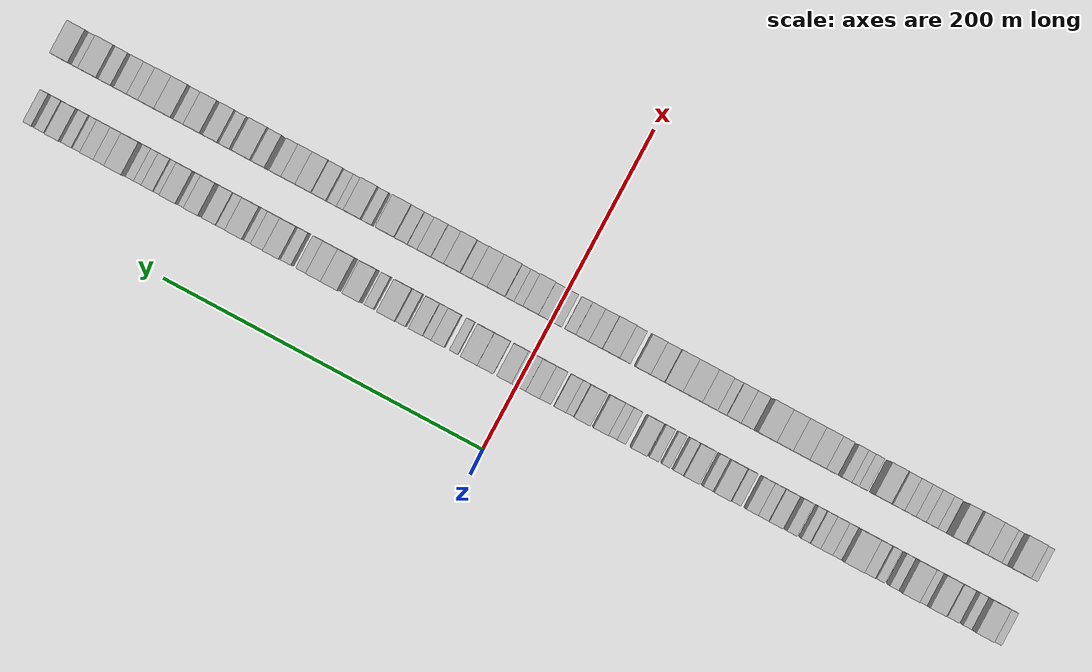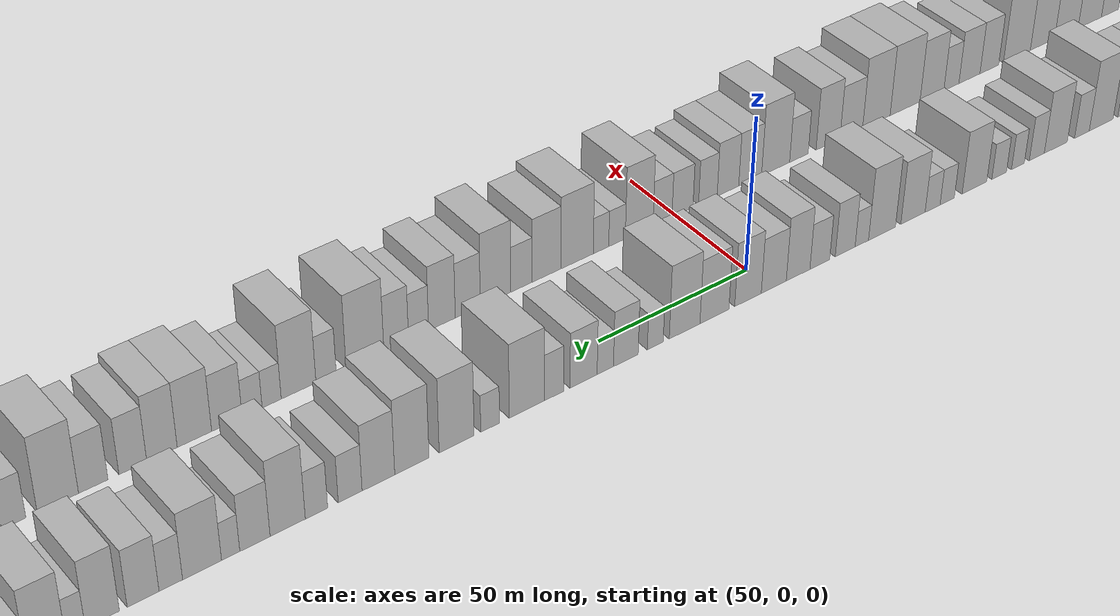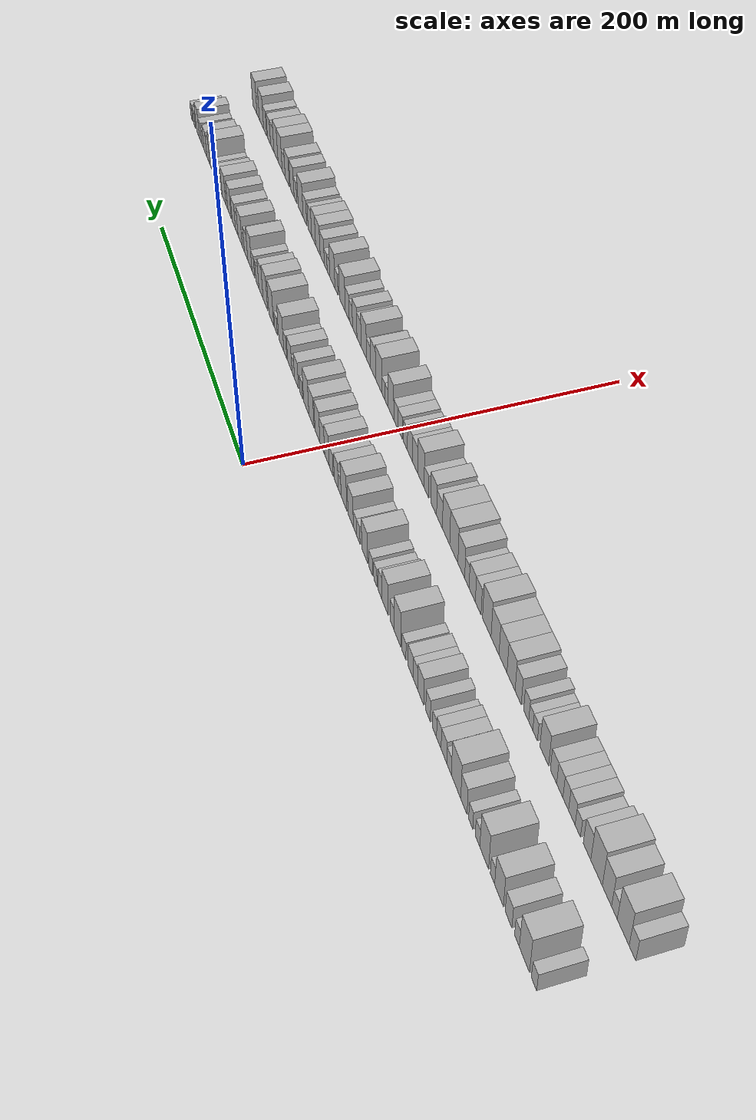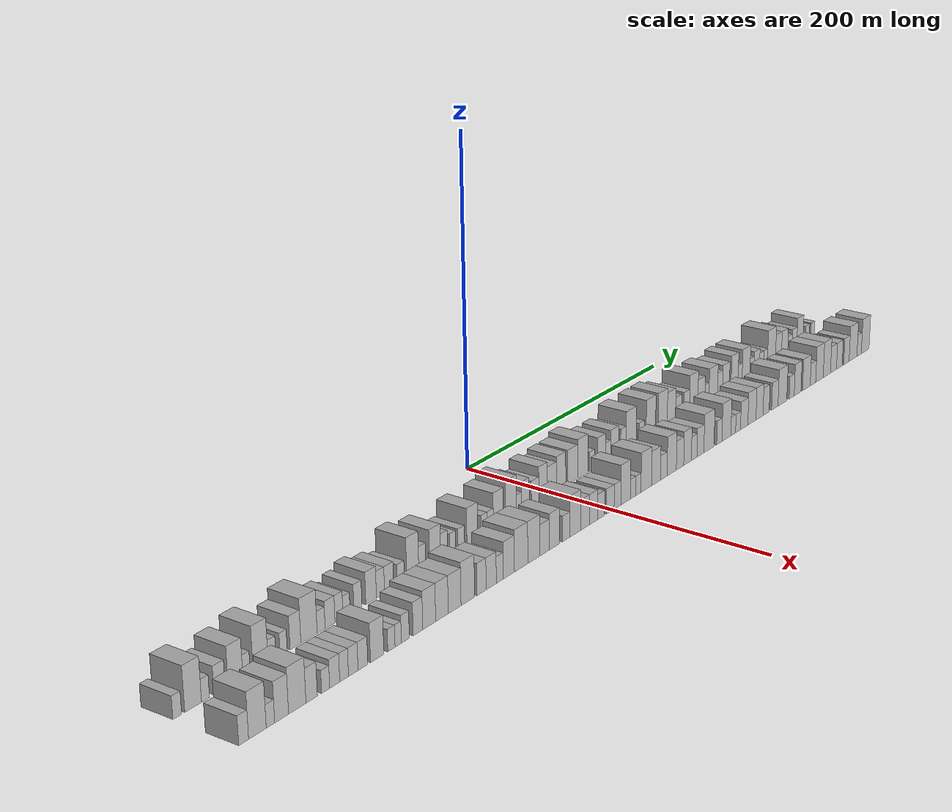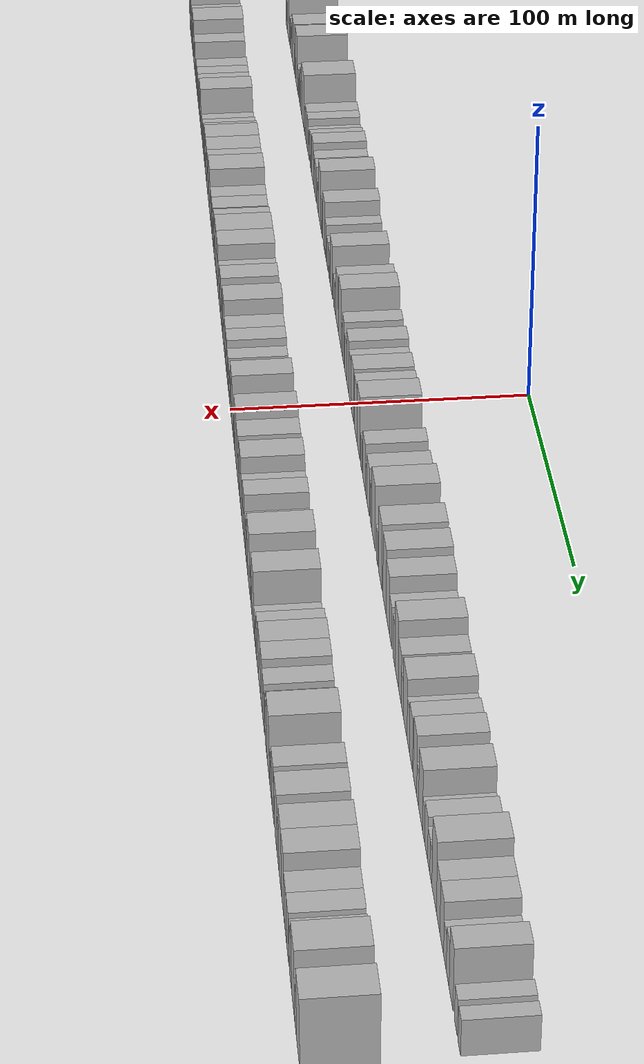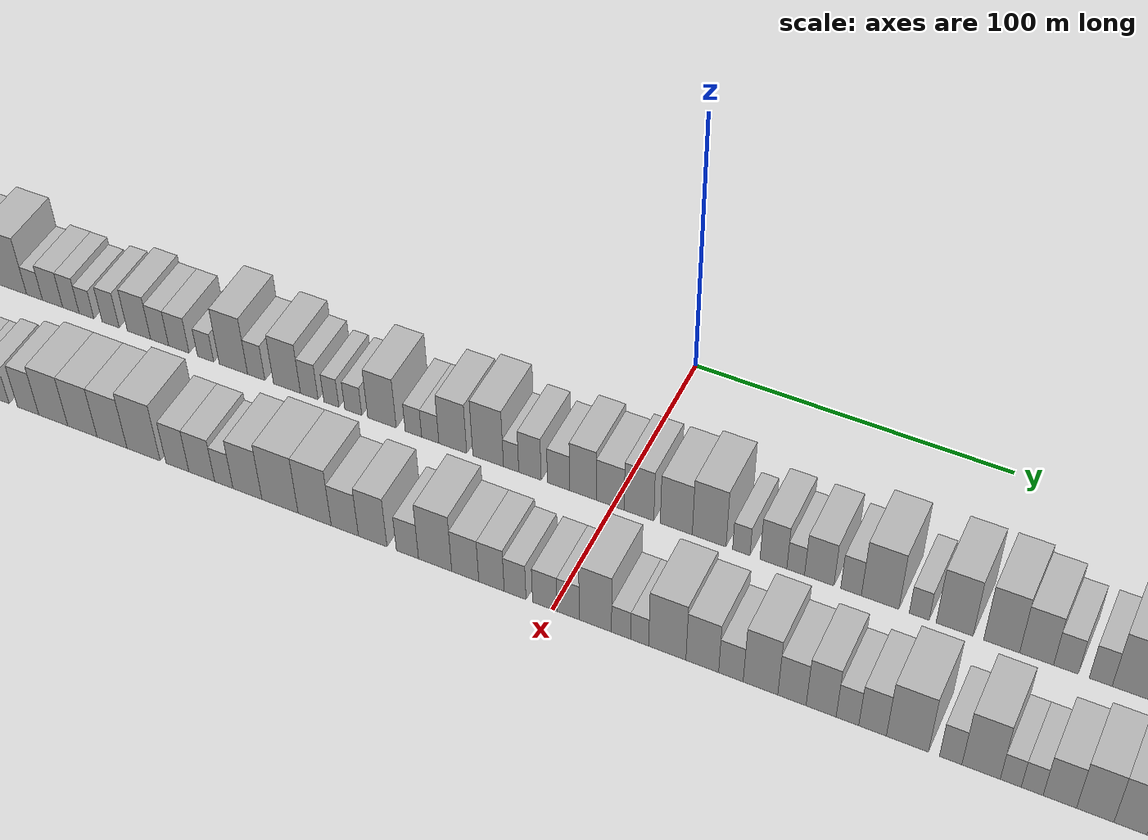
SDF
<sdf version="1.6">
 <world name="default">
  <scene>
   <sky><clouds><speed>12</speed></clouds></sky>
   <ambient>0.4 0.4 0.4 1</ambient>
   <background>0.7 0.7 0.7 1</background>
   <shadows>1</shadows>
  </scene>
  <gravity>0 0 -9.8066</gravity>
  <magnetic_field>6e-06 2.3e-05 -4.2e-05</magnetic_field>
  <physics default="0" name="default_physics" type="ode">
   <ode>
    <solver>
     <type>quick</type>
     <iters>10</iters>
     <sor>1.0</sor>
     <use_dynamic_moi_rescaling>0</use_dynamic_moi_rescaling>
    </solver>
    <constraints>
     <cfm>0</cfm>
     <erp>0.2</erp>
     <contact_max_correcting_vel>100</contact_max_correcting_vel>
     <contact_surface_layer>0.001</contact_surface_layer>
    </constraints>
   </ode>
   <max_step_size>0.004</max_step_size>
   <real_time_factor>1</real_time_factor>
   <real_time_update_rate>250</real_time_update_rate>
  </physics>
  <light name="sun" type="directional">
   <pose>0 0 10 0 0 0</pose>
   <diffuse>0.8 0.8 0.8 1</diffuse>
   <specular>0.2 0.2 0.2 1</specular>
   <attenuation>
    <range>1000</range>
    <constant>0.9</constant>
    <linear>0.01</linear>
    <quadratic>0.001</quadratic>
   </attenuation>
   <direction>-0.5 0.1 -0.9</direction>
  </light>
  <model name="building_1">
   <static>1</static>
   <pose>50.0000 -297.1973 0 0.000000 0.000000 0.000000</pose>
   <link name="link">
    <pose>0 0 6.00 0 0 0</pose>
    <collision name="collision"><geometry><box><size>20.0000 5.6054 12.0000</size></box></geometry></collision>
    <visual name="visual">
     <cast_shadows>0</cast_shadows>
     <geometry><box><size>20.0000 5.6054 12.0000</size></box></geometry>
     <material>
      <script>
       <uri>model://HANNAS_wall/materials/scripts</uri>
       <uri>model://HANNAS_wall/materials/textures</uri>
       <name>vrc/HANNAS_wall</name>
      </script>
     </material>
    </visual>
   </link>
  </model>
  <model name="building_2">
   <static>1</static>
   <pose>50.0000 -286.9371 0 0.000000 0.000000 0.000000</pose>
   <link name="link">
    <pose>0 0 12.00 0 0 0</pose>
    <collision name="collision"><geometry><box><size>20.0000 10.9151 24.0000</size></box></geometry></collision>
    <visual name="visual">
     <cast_shadows>0</cast_shadows>
     <geometry><box><size>20.0000 10.9151 24.0000</size></box></geometry>
     <material>
      <script>
       <uri>model://HANNAS_wall/materials/scripts</uri>
       <uri>model://HANNAS_wall/materials/textures</uri>
       <name>vrc/HANNAS_wall</name>
      </script>
     </material>
    </visual>
   </link>
  </model>
  <model name="building_3">
   <static>1</static>
   <pose>50.0000 -278.8624 0 0.000000 0.000000 0.000000</pose>
   <link name="link">
    <pose>0 0 6.00 0 0 0</pose>
    <collision name="collision"><geometry><box><size>20.0000 5.2342 12.0000</size></box></geometry></collision>
    <visual name="visual">
     <cast_shadows>0</cast_shadows>
     <geometry><box><size>20.0000 5.2342 12.0000</size></box></geometry>
     <material>
      <script>
       <uri>model://HANNAS_wall/materials/scripts</uri>
       <uri>model://HANNAS_wall/materials/textures</uri>
       <name>vrc/HANNAS_wall</name>
      </script>
     </material>
    </visual>
   </link>
  </model>
  <model name="building_4">
   <static>1</static>
   <pose>50.0000 -269.5270 0 0.000000 0.000000 0.000000</pose>
   <link name="link">
    <pose>0 0 7.50 0 0 0</pose>
    <collision name="collision"><geometry><box><size>20.0000 7.4367 15.0000</size></box></geometry></collision>
    <visual name="visual">
     <cast_shadows>0</cast_shadows>
     <geometry><box><size>20.0000 7.4367 15.0000</size></box></geometry>
     <material>
      <script>
       <uri>model://HANNAS_wall/materials/scripts</uri>
       <uri>model://HANNAS_wall/materials/textures</uri>
       <name>vrc/HANNAS_wall</name>
      </script>
     </material>
    </visual>
   </link>
  </model>
  <model name="building_5">
   <static>1</static>
   <pose>50.0000 -258.8061 0 0.000000 0.000000 0.000000</pose>
   <link name="link">
    <pose>0 0 10.50 0 0 0</pose>
    <collision name="collision"><geometry><box><size>20.0000 10.0052 21.0000</size></box></geometry></collision>
    <visual name="visual">
     <cast_shadows>0</cast_shadows>
     <geometry><box><size>20.0000 10.0052 21.0000</size></box></geometry>
     <material>
      <script>
       <uri>model://HANNAS_wall/materials/scripts</uri>
       <uri>model://HANNAS_wall/materials/textures</uri>
       <name>vrc/HANNAS_wall</name>
      </script>
     </material>
    </visual>
   </link>
  </model>
  <model name="building_6">
   <static>1</static>
   <pose>50.0000 -251.2828 0 0.000000 0.000000 0.000000</pose>
   <link name="link">
    <pose>0 0 6.00 0 0 0</pose>
    <collision name="collision"><geometry><box><size>20.0000 5.0414 12.0000</size></box></geometry></collision>
    <visual name="visual">
     <cast_shadows>0</cast_shadows>
     <geometry><box><size>20.0000 5.0414 12.0000</size></box></geometry>
     <material>
      <script>
       <uri>model://HANNAS_wall/materials/scripts</uri>
       <uri>model://HANNAS_wall/materials/textures</uri>
       <name>vrc/HANNAS_wall</name>
      </script>
     </material>
    </visual>
   </link>
  </model>
  <model name="building_7">
   <static>1</static>
   <pose>50.0000 -241.5518 0 0.000000 0.000000 0.000000</pose>
   <link name="link">
    <pose>0 0 12.00 0 0 0</pose>
    <collision name="collision"><geometry><box><size>20.0000 10.4205 24.0000</size></box></geometry></collision>
    <visual name="visual">
     <cast_shadows>0</cast_shadows>
     <geometry><box><size>20.0000 10.4205 24.0000</size></box></geometry>
     <material>
      <script>
       <uri>model://HANNAS_wall/materials/scripts</uri>
       <uri>model://HANNAS_wall/materials/textures</uri>
       <name>vrc/HANNAS_wall</name>
      </script>
     </material>
    </visual>
   </link>
  </model>
  <model name="building_8">
   <static>1</static>
   <pose>50.0000 -233.5852 0 0.000000 0.000000 0.000000</pose>
   <link name="link">
    <pose>0 0 6.00 0 0 0</pose>
    <collision name="collision"><geometry><box><size>20.0000 5.5127 12.0000</size></box></geometry></collision>
    <visual name="visual">
     <cast_shadows>0</cast_shadows>
     <geometry><box><size>20.0000 5.5127 12.0000</size></box></geometry>
     <material>
      <script>
       <uri>model://HANNAS_wall/materials/scripts</uri>
       <uri>model://HANNAS_wall/materials/textures</uri>
       <name>vrc/HANNAS_wall</name>
      </script>
     </material>
    </visual>
   </link>
  </model>
  <model name="building_9">
   <static>1</static>
   <pose>50.0000 -225.2683 0 0.000000 0.000000 0.000000</pose>
   <link name="link">
    <pose>0 0 6.00 0 0 0</pose>
    <collision name="collision"><geometry><box><size>20.0000 5.1211 12.0000</size></box></geometry></collision>
    <visual name="visual">
     <cast_shadows>0</cast_shadows>
     <geometry><box><size>20.0000 5.1211 12.0000</size></box></geometry>
     <material>
      <script>
       <uri>model://HANNAS_wall/materials/scripts</uri>
       <uri>model://HANNAS_wall/materials/textures</uri>
       <name>vrc/HANNAS_wall</name>
      </script>
     </material>
    </visual>
   </link>
  </model>
  <model name="building_10">
   <static>1</static>
   <pose>50.0000 -216.8005 0 0.000000 0.000000 0.000000</pose>
   <link name="link">
    <pose>0 0 9.00 0 0 0</pose>
    <collision name="collision"><geometry><box><size>20.0000 7.8146 18.0000</size></box></geometry></collision>
    <visual name="visual">
     <cast_shadows>0</cast_shadows>
     <geometry><box><size>20.0000 7.8146 18.0000</size></box></geometry>
     <material>
      <script>
       <uri>model://HANNAS_wall/materials/scripts</uri>
       <uri>model://HANNAS_wall/materials/textures</uri>
       <name>vrc/HANNAS_wall</name>
      </script>
     </material>
    </visual>
   </link>
  </model>
  <model name="building_11">
   <static>1</static>
   <pose>50.0000 -206.9055 0 0.000000 0.000000 0.000000</pose>
   <link name="link">
    <pose>0 0 12.00 0 0 0</pose>
    <collision name="collision"><geometry><box><size>20.0000 11.9755 24.0000</size></box></geometry></collision>
    <visual name="visual">
     <cast_shadows>0</cast_shadows>
     <geometry><box><size>20.0000 11.9755 24.0000</size></box></geometry>
     <material>
      <script>
       <uri>model://HANNAS_wall/materials/scripts</uri>
       <uri>model://HANNAS_wall/materials/textures</uri>
       <name>vrc/HANNAS_wall</name>
      </script>
     </material>
    </visual>
   </link>
  </model>
  <model name="building_12">
   <static>1</static>
   <pose>50.0000 -197.9457 0 0.000000 0.000000 0.000000</pose>
   <link name="link">
    <pose>0 0 6.00 0 0 0</pose>
    <collision name="collision"><geometry><box><size>20.0000 5.9440 12.0000</size></box></geometry></collision>
    <visual name="visual">
     <cast_shadows>0</cast_shadows>
     <geometry><box><size>20.0000 5.9440 12.0000</size></box></geometry>
     <material>
      <script>
       <uri>model://HANNAS_wall/materials/scripts</uri>
       <uri>model://HANNAS_wall/materials/textures</uri>
       <name>vrc/HANNAS_wall</name>
      </script>
     </material>
    </visual>
   </link>
  </model>
  <model name="building_13">
   <static>1</static>
   <pose>50.0000 -191.2312 0 0.000000 0.000000 0.000000</pose>
   <link name="link">
    <pose>0 0 7.50 0 0 0</pose>
    <collision name="collision"><geometry><box><size>20.0000 7.4850 15.0000</size></box></geometry></collision>
    <visual name="visual">
     <cast_shadows>0</cast_shadows>
     <geometry><box><size>20.0000 7.4850 15.0000</size></box></geometry>
     <material>
      <script>
       <uri>model://HANNAS_wall/materials/scripts</uri>
       <uri>model://HANNAS_wall/materials/textures</uri>
       <name>vrc/HANNAS_wall</name>
      </script>
     </material>
    </visual>
   </link>
  </model>
  <model name="building_14">
   <static>1</static>
   <pose>50.0000 -184.4612 0 0.000000 0.000000 0.000000</pose>
   <link name="link">
    <pose>0 0 7.50 0 0 0</pose>
    <collision name="collision"><geometry><box><size>20.0000 6.0550 15.0000</size></box></geometry></collision>
    <visual name="visual">
     <cast_shadows>0</cast_shadows>
     <geometry><box><size>20.0000 6.0550 15.0000</size></box></geometry>
     <material>
      <script>
       <uri>model://HANNAS_wall/materials/scripts</uri>
       <uri>model://HANNAS_wall/materials/textures</uri>
       <name>vrc/HANNAS_wall</name>
      </script>
     </material>
    </visual>
   </link>
  </model>
  <model name="building_15">
   <static>1</static>
   <pose>50.0000 -178.7325 0 0.000000 0.000000 0.000000</pose>
   <link name="link">
    <pose>0 0 6.00 0 0 0</pose>
    <collision name="collision"><geometry><box><size>20.0000 5.4024 12.0000</size></box></geometry></collision>
    <visual name="visual">
     <cast_shadows>0</cast_shadows>
     <geometry><box><size>20.0000 5.4024 12.0000</size></box></geometry>
     <material>
      <script>
       <uri>model://HANNAS_wall/materials/scripts</uri>
       <uri>model://HANNAS_wall/materials/textures</uri>
       <name>vrc/HANNAS_wall</name>
      </script>
     </material>
    </visual>
   </link>
  </model>
  <model name="building_16">
   <static>1</static>
   <pose>50.0000 -169.9344 0 0.000000 0.000000 0.000000</pose>
   <link name="link">
    <pose>0 0 7.50 0 0 0</pose>
    <collision name="collision"><geometry><box><size>20.0000 6.1939 15.0000</size></box></geometry></collision>
    <visual name="visual">
     <cast_shadows>0</cast_shadows>
     <geometry><box><size>20.0000 6.1939 15.0000</size></box></geometry>
     <material>
      <script>
       <uri>model://HANNAS_wall/materials/scripts</uri>
       <uri>model://HANNAS_wall/materials/textures</uri>
       <name>vrc/HANNAS_wall</name>
      </script>
     </material>
    </visual>
   </link>
  </model>
  <model name="building_17">
   <static>1</static>
   <pose>50.0000 -159.6488 0 0.000000 0.000000 0.000000</pose>
   <link name="link">
    <pose>0 0 9.00 0 0 0</pose>
    <collision name="collision"><geometry><box><size>20.0000 8.3773 18.0000</size></box></geometry></collision>
    <visual name="visual">
     <cast_shadows>0</cast_shadows>
     <geometry><box><size>20.0000 8.3773 18.0000</size></box></geometry>
     <material>
      <script>
       <uri>model://HANNAS_wall/materials/scripts</uri>
       <uri>model://HANNAS_wall/materials/textures</uri>
       <name>vrc/HANNAS_wall</name>
      </script>
     </material>
    </visual>
   </link>
  </model>
  <model name="building_18">
   <static>1</static>
   <pose>50.0000 -152.2264 0 0.000000 0.000000 0.000000</pose>
   <link name="link">
    <pose>0 0 7.50 0 0 0</pose>
    <collision name="collision"><geometry><box><size>20.0000 6.4675 15.0000</size></box></geometry></collision>
    <visual name="visual">
     <cast_shadows>0</cast_shadows>
     <geometry><box><size>20.0000 6.4675 15.0000</size></box></geometry>
     <material>
      <script>
       <uri>model://HANNAS_wall/materials/scripts</uri>
       <uri>model://HANNAS_wall/materials/textures</uri>
       <name>vrc/HANNAS_wall</name>
      </script>
     </material>
    </visual>
   </link>
  </model>
  <model name="building_19">
   <static>1</static>
   <pose>50.0000 -145.3446 0 0.000000 0.000000 0.000000</pose>
   <link name="link">
    <pose>0 0 7.50 0 0 0</pose>
    <collision name="collision"><geometry><box><size>20.0000 7.2962 15.0000</size></box></geometry></collision>
    <visual name="visual">
     <cast_shadows>0</cast_shadows>
     <geometry><box><size>20.0000 7.2962 15.0000</size></box></geometry>
     <material>
      <script>
       <uri>model://HANNAS_wall/materials/scripts</uri>
       <uri>model://HANNAS_wall/materials/textures</uri>
       <name>vrc/HANNAS_wall</name>
      </script>
     </material>
    </visual>
   </link>
  </model>
  <model name="building_20">
   <static>1</static>
   <pose>50.0000 -135.8455 0 0.000000 0.000000 0.000000</pose>
   <link name="link">
    <pose>0 0 6.00 0 0 0</pose>
    <collision name="collision"><geometry><box><size>20.0000 5.7019 12.0000</size></box></geometry></collision>
    <visual name="visual">
     <cast_shadows>0</cast_shadows>
     <geometry><box><size>20.0000 5.7019 12.0000</size></box></geometry>
     <material>
      <script>
       <uri>model://HANNAS_wall/materials/scripts</uri>
       <uri>model://HANNAS_wall/materials/textures</uri>
       <name>vrc/HANNAS_wall</name>
      </script>
     </material>
    </visual>
   </link>
  </model>
  <model name="building_21">
   <static>1</static>
   <pose>50.0000 -126.0394 0 0.000000 0.000000 0.000000</pose>
   <link name="link">
    <pose>0 0 12.00 0 0 0</pose>
    <collision name="collision"><geometry><box><size>20.0000 9.9102 24.0000</size></box></geometry></collision>
    <visual name="visual">
     <cast_shadows>0</cast_shadows>
     <geometry><box><size>20.0000 9.9102 24.0000</size></box></geometry>
     <material>
      <script>
       <uri>model://HANNAS_wall/materials/scripts</uri>
       <uri>model://HANNAS_wall/materials/textures</uri>
       <name>vrc/HANNAS_wall</name>
      </script>
     </material>
    </visual>
   </link>
  </model>
  <model name="building_22">
   <static>1</static>
   <pose>50.0000 -118.0736 0 0.000000 0.000000 0.000000</pose>
   <link name="link">
    <pose>0 0 7.50 0 0 0</pose>
    <collision name="collision"><geometry><box><size>20.0000 6.0215 15.0000</size></box></geometry></collision>
    <visual name="visual">
     <cast_shadows>0</cast_shadows>
     <geometry><box><size>20.0000 6.0215 15.0000</size></box></geometry>
     <material>
      <script>
       <uri>model://HANNAS_wall/materials/scripts</uri>
       <uri>model://HANNAS_wall/materials/textures</uri>
       <name>vrc/HANNAS_wall</name>
      </script>
     </material>
    </visual>
   </link>
  </model>
  <model name="building_23">
   <static>1</static>
   <pose>50.0000 -107.4133 0 0.000000 0.000000 0.000000</pose>
   <link name="link">
    <pose>0 0 10.50 0 0 0</pose>
    <collision name="collision"><geometry><box><size>20.0000 9.2990 21.0000</size></box></geometry></collision>
    <visual name="visual">
     <cast_shadows>0</cast_shadows>
     <geometry><box><size>20.0000 9.2990 21.0000</size></box></geometry>
     <material>
      <script>
       <uri>model://HANNAS_wall/materials/scripts</uri>
       <uri>model://HANNAS_wall/materials/textures</uri>
       <name>vrc/HANNAS_wall</name>
      </script>
     </material>
    </visual>
   </link>
  </model>
  <model name="building_24">
   <static>1</static>
   <pose>50.0000 -99.7550 0 0.000000 0.000000 0.000000</pose>
   <link name="link">
    <pose>0 0 7.50 0 0 0</pose>
    <collision name="collision"><geometry><box><size>20.0000 6.0176 15.0000</size></box></geometry></collision>
    <visual name="visual">
     <cast_shadows>0</cast_shadows>
     <geometry><box><size>20.0000 6.0176 15.0000</size></box></geometry>
     <material>
      <script>
       <uri>model://HANNAS_wall/materials/scripts</uri>
       <uri>model://HANNAS_wall/materials/textures</uri>
       <name>vrc/HANNAS_wall</name>
      </script>
     </material>
    </visual>
   </link>
  </model>
  <model name="building_25">
   <static>1</static>
   <pose>50.0000 -92.1950 0 0.000000 0.000000 0.000000</pose>
   <link name="link">
    <pose>0 0 6.00 0 0 0</pose>
    <collision name="collision"><geometry><box><size>20.0000 5.1025 12.0000</size></box></geometry></collision>
    <visual name="visual">
     <cast_shadows>0</cast_shadows>
     <geometry><box><size>20.0000 5.1025 12.0000</size></box></geometry>
     <material>
      <script>
       <uri>model://HANNAS_wall/materials/scripts</uri>
       <uri>model://HANNAS_wall/materials/textures</uri>
       <name>vrc/HANNAS_wall</name>
      </script>
     </material>
    </visual>
   </link>
  </model>
  <model name="building_26">
   <static>1</static>
   <pose>50.0000 -84.7635 0 0.000000 0.000000 0.000000</pose>
   <link name="link">
    <pose>0 0 6.00 0 0 0</pose>
    <collision name="collision"><geometry><box><size>20.0000 5.7605 12.0000</size></box></geometry></collision>
    <visual name="visual">
     <cast_shadows>0</cast_shadows>
     <geometry><box><size>20.0000 5.7605 12.0000</size></box></geometry>
     <material>
      <script>
       <uri>model://HANNAS_wall/materials/scripts</uri>
       <uri>model://HANNAS_wall/materials/textures</uri>
       <name>vrc/HANNAS_wall</name>
      </script>
     </material>
    </visual>
   </link>
  </model>
  <model name="building_27">
   <static>1</static>
   <pose>50.0000 -75.1036 0 0.000000 0.000000 0.000000</pose>
   <link name="link">
    <pose>0 0 10.50 0 0 0</pose>
    <collision name="collision"><geometry><box><size>20.0000 9.5592 21.0000</size></box></geometry></collision>
    <visual name="visual">
     <cast_shadows>0</cast_shadows>
     <geometry><box><size>20.0000 9.5592 21.0000</size></box></geometry>
     <material>
      <script>
       <uri>model://HANNAS_wall/materials/scripts</uri>
       <uri>model://HANNAS_wall/materials/textures</uri>
       <name>vrc/HANNAS_wall</name>
      </script>
     </material>
    </visual>
   </link>
  </model>
  <model name="building_28">
   <static>1</static>
   <pose>50.0000 -64.5935 0 0.000000 0.000000 0.000000</pose>
   <link name="link">
    <pose>0 0 6.00 0 0 0</pose>
    <collision name="collision"><geometry><box><size>20.0000 5.4610 12.0000</size></box></geometry></collision>
    <visual name="visual">
     <cast_shadows>0</cast_shadows>
     <geometry><box><size>20.0000 5.4610 12.0000</size></box></geometry>
     <material>
      <script>
       <uri>model://HANNAS_wall/materials/scripts</uri>
       <uri>model://HANNAS_wall/materials/textures</uri>
       <name>vrc/HANNAS_wall</name>
      </script>
     </material>
    </visual>
   </link>
  </model>
  <model name="building_29">
   <static>1</static>
   <pose>50.0000 -59.0190 0 0.000000 0.000000 0.000000</pose>
   <link name="link">
    <pose>0 0 6.00 0 0 0</pose>
    <collision name="collision"><geometry><box><size>20.0000 5.6881 12.0000</size></box></geometry></collision>
    <visual name="visual">
     <cast_shadows>0</cast_shadows>
     <geometry><box><size>20.0000 5.6881 12.0000</size></box></geometry>
     <material>
      <script>
       <uri>model://HANNAS_wall/materials/scripts</uri>
       <uri>model://HANNAS_wall/materials/textures</uri>
       <name>vrc/HANNAS_wall</name>
      </script>
     </material>
    </visual>
   </link>
  </model>
  <model name="building_30">
   <static>1</static>
   <pose>50.0000 -51.6029 0 0.000000 0.000000 0.000000</pose>
   <link name="link">
    <pose>0 0 10.50 0 0 0</pose>
    <collision name="collision"><geometry><box><size>20.0000 9.1441 21.0000</size></box></geometry></collision>
    <visual name="visual">
     <cast_shadows>0</cast_shadows>
     <geometry><box><size>20.0000 9.1441 21.0000</size></box></geometry>
     <material>
      <script>
       <uri>model://HANNAS_wall/materials/scripts</uri>
       <uri>model://HANNAS_wall/materials/textures</uri>
       <name>vrc/HANNAS_wall</name>
      </script>
     </material>
    </visual>
   </link>
  </model>
  <model name="building_31">
   <static>1</static>
   <pose>50.0000 -40.0426 0 0.000000 0.000000 0.000000</pose>
   <link name="link">
    <pose>0 0 12.00 0 0 0</pose>
    <collision name="collision"><geometry><box><size>20.0000 9.9766 24.0000</size></box></geometry></collision>
    <visual name="visual">
     <cast_shadows>0</cast_shadows>
     <geometry><box><size>20.0000 9.9766 24.0000</size></box></geometry>
     <material>
      <script>
       <uri>model://HANNAS_wall/materials/scripts</uri>
       <uri>model://HANNAS_wall/materials/textures</uri>
       <name>vrc/HANNAS_wall</name>
      </script>
     </material>
    </visual>
   </link>
  </model>
  <model name="building_32">
   <static>1</static>
   <pose>50.0000 -32.5910 0 0.000000 0.000000 0.000000</pose>
   <link name="link">
    <pose>0 0 6.00 0 0 0</pose>
    <collision name="collision"><geometry><box><size>20.0000 4.9266 12.0000</size></box></geometry></collision>
    <visual name="visual">
     <cast_shadows>0</cast_shadows>
     <geometry><box><size>20.0000 4.9266 12.0000</size></box></geometry>
     <material>
      <script>
       <uri>model://HANNAS_wall/materials/scripts</uri>
       <uri>model://HANNAS_wall/materials/textures</uri>
       <name>vrc/HANNAS_wall</name>
      </script>
     </material>
    </visual>
   </link>
  </model>
  <model name="building_33">
   <static>1</static>
   <pose>50.0000 -26.5214 0 0.000000 0.000000 0.000000</pose>
   <link name="link">
    <pose>0 0 9.00 0 0 0</pose>
    <collision name="collision"><geometry><box><size>20.0000 7.2126 18.0000</size></box></geometry></collision>
    <visual name="visual">
     <cast_shadows>0</cast_shadows>
     <geometry><box><size>20.0000 7.2126 18.0000</size></box></geometry>
     <material>
      <script>
       <uri>model://HANNAS_wall/materials/scripts</uri>
       <uri>model://HANNAS_wall/materials/textures</uri>
       <name>vrc/HANNAS_wall</name>
      </script>
     </material>
    </visual>
   </link>
  </model>
  <model name="building_34">
   <static>1</static>
   <pose>50.0000 -17.3667 0 0.000000 0.000000 0.000000</pose>
   <link name="link">
    <pose>0 0 7.50 0 0 0</pose>
    <collision name="collision"><geometry><box><size>20.0000 7.0967 15.0000</size></box></geometry></collision>
    <visual name="visual">
     <cast_shadows>0</cast_shadows>
     <geometry><box><size>20.0000 7.0967 15.0000</size></box></geometry>
     <material>
      <script>
       <uri>model://HANNAS_wall/materials/scripts</uri>
       <uri>model://HANNAS_wall/materials/textures</uri>
       <name>vrc/HANNAS_wall</name>
      </script>
     </material>
    </visual>
   </link>
  </model>
  <model name="building_35">
   <static>1</static>
   <pose>50.0000 -9.6184 0 0.000000 0.000000 0.000000</pose>
   <link name="link">
    <pose>0 0 10.50 0 0 0</pose>
    <collision name="collision"><geometry><box><size>20.0000 8.4000 21.0000</size></box></geometry></collision>
    <visual name="visual">
     <cast_shadows>0</cast_shadows>
     <geometry><box><size>20.0000 8.4000 21.0000</size></box></geometry>
     <material>
      <script>
       <uri>model://HANNAS_wall/materials/scripts</uri>
       <uri>model://HANNAS_wall/materials/textures</uri>
       <name>vrc/HANNAS_wall</name>
      </script>
     </material>
    </visual>
   </link>
  </model>
  <model name="building_36">
   <static>1</static>
   <pose>50.0000 -1.0348 0 0.000000 0.000000 0.000000</pose>
   <link name="link">
    <pose>0 0 9.00 0 0 0</pose>
    <collision name="collision"><geometry><box><size>20.0000 8.7670 18.0000</size></box></geometry></collision>
    <visual name="visual">
     <cast_shadows>0</cast_shadows>
     <geometry><box><size>20.0000 8.7670 18.0000</size></box></geometry>
     <material>
      <script>
       <uri>model://HANNAS_wall/materials/scripts</uri>
       <uri>model://HANNAS_wall/materials/textures</uri>
       <name>vrc/HANNAS_wall</name>
      </script>
     </material>
    </visual>
   </link>
  </model>
  <model name="building_37">
   <static>1</static>
   <pose>50.0000 7.9456 0 0.000000 0.000000 0.000000</pose>
   <link name="link">
    <pose>0 0 10.50 0 0 0</pose>
    <collision name="collision"><geometry><box><size>20.0000 9.1939 21.0000</size></box></geometry></collision>
    <visual name="visual">
     <cast_shadows>0</cast_shadows>
     <geometry><box><size>20.0000 9.1939 21.0000</size></box></geometry>
     <material>
      <script>
       <uri>model://HANNAS_wall/materials/scripts</uri>
       <uri>model://HANNAS_wall/materials/textures</uri>
       <name>vrc/HANNAS_wall</name>
      </script>
     </material>
    </visual>
   </link>
  </model>
  <model name="building_38">
   <static>1</static>
   <pose>50.0000 19.4693 0 0.000000 0.000000 0.000000</pose>
   <link name="link">
    <pose>0 0 10.50 0 0 0</pose>
    <collision name="collision"><geometry><box><size>20.0000 9.8533 21.0000</size></box></geometry></collision>
    <visual name="visual">
     <cast_shadows>0</cast_shadows>
     <geometry><box><size>20.0000 9.8533 21.0000</size></box></geometry>
     <material>
      <script>
       <uri>model://HANNAS_wall/materials/scripts</uri>
       <uri>model://HANNAS_wall/materials/textures</uri>
       <name>vrc/HANNAS_wall</name>
      </script>
     </material>
    </visual>
   </link>
  </model>
  <model name="building_39">
   <static>1</static>
   <pose>50.0000 29.5468 0 0.000000 0.000000 0.000000</pose>
   <link name="link">
    <pose>0 0 12.00 0 0 0</pose>
    <collision name="collision"><geometry><box><size>20.0000 10.3018 24.0000</size></box></geometry></collision>
    <visual name="visual">
     <cast_shadows>0</cast_shadows>
     <geometry><box><size>20.0000 10.3018 24.0000</size></box></geometry>
     <material>
      <script>
       <uri>model://HANNAS_wall/materials/scripts</uri>
       <uri>model://HANNAS_wall/materials/textures</uri>
       <name>vrc/HANNAS_wall</name>
      </script>
     </material>
    </visual>
   </link>
  </model>
  <model name="building_40">
   <static>1</static>
   <pose>50.0000 39.3319 0 0.000000 0.000000 0.000000</pose>
   <link name="link">
    <pose>0 0 6.00 0 0 0</pose>
    <collision name="collision"><geometry><box><size>20.0000 5.2682 12.0000</size></box></geometry></collision>
    <visual name="visual">
     <cast_shadows>0</cast_shadows>
     <geometry><box><size>20.0000 5.2682 12.0000</size></box></geometry>
     <material>
      <script>
       <uri>model://HANNAS_wall/materials/scripts</uri>
       <uri>model://HANNAS_wall/materials/textures</uri>
       <name>vrc/HANNAS_wall</name>
      </script>
     </material>
    </visual>
   </link>
  </model>
  <model name="building_41">
   <static>1</static>
   <pose>50.0000 48.9914 0 0.000000 0.000000 0.000000</pose>
   <link name="link">
    <pose>0 0 9.00 0 0 0</pose>
    <collision name="collision"><geometry><box><size>20.0000 8.0509 18.0000</size></box></geometry></collision>
    <visual name="visual">
     <cast_shadows>0</cast_shadows>
     <geometry><box><size>20.0000 8.0509 18.0000</size></box></geometry>
     <material>
      <script>
       <uri>model://HANNAS_wall/materials/scripts</uri>
       <uri>model://HANNAS_wall/materials/textures</uri>
       <name>vrc/HANNAS_wall</name>
      </script>
     </material>
    </visual>
   </link>
  </model>
  <model name="building_42">
   <static>1</static>
   <pose>50.0000 55.6602 0 0.000000 0.000000 0.000000</pose>
   <link name="link">
    <pose>0 0 6.00 0 0 0</pose>
    <collision name="collision"><geometry><box><size>20.0000 5.2866 12.0000</size></box></geometry></collision>
    <visual name="visual">
     <cast_shadows>0</cast_shadows>
     <geometry><box><size>20.0000 5.2866 12.0000</size></box></geometry>
     <material>
      <script>
       <uri>model://HANNAS_wall/materials/scripts</uri>
       <uri>model://HANNAS_wall/materials/textures</uri>
       <name>vrc/HANNAS_wall</name>
      </script>
     </material>
    </visual>
   </link>
  </model>
  <model name="building_43">
   <static>1</static>
   <pose>50.0000 62.6468 0 0.000000 0.000000 0.000000</pose>
   <link name="link">
    <pose>0 0 9.00 0 0 0</pose>
    <collision name="collision"><geometry><box><size>20.0000 8.6865 18.0000</size></box></geometry></collision>
    <visual name="visual">
     <cast_shadows>0</cast_shadows>
     <geometry><box><size>20.0000 8.6865 18.0000</size></box></geometry>
     <material>
      <script>
       <uri>model://HANNAS_wall/materials/scripts</uri>
       <uri>model://HANNAS_wall/materials/textures</uri>
       <name>vrc/HANNAS_wall</name>
      </script>
     </material>
    </visual>
   </link>
  </model>
  <model name="building_44">
   <static>1</static>
   <pose>50.0000 72.0212 0 0.000000 0.000000 0.000000</pose>
   <link name="link">
    <pose>0 0 7.50 0 0 0</pose>
    <collision name="collision"><geometry><box><size>20.0000 6.0623 15.0000</size></box></geometry></collision>
    <visual name="visual">
     <cast_shadows>0</cast_shadows>
     <geometry><box><size>20.0000 6.0623 15.0000</size></box></geometry>
     <material>
      <script>
       <uri>model://HANNAS_wall/materials/scripts</uri>
       <uri>model://HANNAS_wall/materials/textures</uri>
       <name>vrc/HANNAS_wall</name>
      </script>
     </material>
    </visual>
   </link>
  </model>
  <model name="building_45">
   <static>1</static>
   <pose>50.0000 80.5206 0 0.000000 0.000000 0.000000</pose>
   <link name="link">
    <pose>0 0 12.00 0 0 0</pose>
    <collision name="collision"><geometry><box><size>20.0000 10.9365 24.0000</size></box></geometry></collision>
    <visual name="visual">
     <cast_shadows>0</cast_shadows>
     <geometry><box><size>20.0000 10.9365 24.0000</size></box></geometry>
     <material>
      <script>
       <uri>model://HANNAS_wall/materials/scripts</uri>
       <uri>model://HANNAS_wall/materials/textures</uri>
       <name>vrc/HANNAS_wall</name>
      </script>
     </material>
    </visual>
   </link>
  </model>
  <model name="building_46">
   <static>1</static>
   <pose>50.0000 91.8539 0 0.000000 0.000000 0.000000</pose>
   <link name="link">
    <pose>0 0 6.00 0 0 0</pose>
    <collision name="collision"><geometry><box><size>20.0000 5.7302 12.0000</size></box></geometry></collision>
    <visual name="visual">
     <cast_shadows>0</cast_shadows>
     <geometry><box><size>20.0000 5.7302 12.0000</size></box></geometry>
     <material>
      <script>
       <uri>model://HANNAS_wall/materials/scripts</uri>
       <uri>model://HANNAS_wall/materials/textures</uri>
       <name>vrc/HANNAS_wall</name>
      </script>
     </material>
    </visual>
   </link>
  </model>
  <model name="building_47">
   <static>1</static>
   <pose>50.0000 101.9800 0 0.000000 0.000000 0.000000</pose>
   <link name="link">
    <pose>0 0 12.00 0 0 0</pose>
    <collision name="collision"><geometry><box><size>20.0000 10.5220 24.0000</size></box></geometry></collision>
    <visual name="visual">
     <cast_shadows>0</cast_shadows>
     <geometry><box><size>20.0000 10.5220 24.0000</size></box></geometry>
     <material>
      <script>
       <uri>model://HANNAS_wall/materials/scripts</uri>
       <uri>model://HANNAS_wall/materials/textures</uri>
       <name>vrc/HANNAS_wall</name>
      </script>
     </material>
    </visual>
   </link>
  </model>
  <model name="building_48">
   <static>1</static>
   <pose>50.0000 115.3014 0 0.000000 0.000000 0.000000</pose>
   <link name="link">
    <pose>0 0 12.00 0 0 0</pose>
    <collision name="collision"><geometry><box><size>20.0000 10.1207 24.0000</size></box></geometry></collision>
    <visual name="visual">
     <cast_shadows>0</cast_shadows>
     <geometry><box><size>20.0000 10.1207 24.0000</size></box></geometry>
     <material>
      <script>
       <uri>model://HANNAS_wall/materials/scripts</uri>
       <uri>model://HANNAS_wall/materials/textures</uri>
       <name>vrc/HANNAS_wall</name>
      </script>
     </material>
    </visual>
   </link>
  </model>
  <model name="building_49">
   <static>1</static>
   <pose>50.0000 125.1056 0 0.000000 0.000000 0.000000</pose>
   <link name="link">
    <pose>0 0 10.50 0 0 0</pose>
    <collision name="collision"><geometry><box><size>20.0000 9.4878 21.0000</size></box></geometry></collision>
    <visual name="visual">
     <cast_shadows>0</cast_shadows>
     <geometry><box><size>20.0000 9.4878 21.0000</size></box></geometry>
     <material>
      <script>
       <uri>model://HANNAS_wall/materials/scripts</uri>
       <uri>model://HANNAS_wall/materials/textures</uri>
       <name>vrc/HANNAS_wall</name>
      </script>
     </material>
    </visual>
   </link>
  </model>
  <model name="building_50">
   <static>1</static>
   <pose>50.0000 133.2721 0 0.000000 0.000000 0.000000</pose>
   <link name="link">
    <pose>0 0 7.50 0 0 0</pose>
    <collision name="collision"><geometry><box><size>20.0000 6.8451 15.0000</size></box></geometry></collision>
    <visual name="visual">
     <cast_shadows>0</cast_shadows>
     <geometry><box><size>20.0000 6.8451 15.0000</size></box></geometry>
     <material>
      <script>
       <uri>model://HANNAS_wall/materials/scripts</uri>
       <uri>model://HANNAS_wall/materials/textures</uri>
       <name>vrc/HANNAS_wall</name>
      </script>
     </material>
    </visual>
   </link>
  </model>
  <model name="building_51">
   <static>1</static>
   <pose>50.0000 142.8507 0 0.000000 0.000000 0.000000</pose>
   <link name="link">
    <pose>0 0 7.50 0 0 0</pose>
    <collision name="collision"><geometry><box><size>20.0000 6.3121 15.0000</size></box></geometry></collision>
    <visual name="visual">
     <cast_shadows>0</cast_shadows>
     <geometry><box><size>20.0000 6.3121 15.0000</size></box></geometry>
     <material>
      <script>
       <uri>model://HANNAS_wall/materials/scripts</uri>
       <uri>model://HANNAS_wall/materials/textures</uri>
       <name>vrc/HANNAS_wall</name>
      </script>
     </material>
    </visual>
   </link>
  </model>
  <model name="building_52">
   <static>1</static>
   <pose>50.0000 150.9185 0 0.000000 0.000000 0.000000</pose>
   <link name="link">
    <pose>0 0 12.00 0 0 0</pose>
    <collision name="collision"><geometry><box><size>20.0000 9.8236 24.0000</size></box></geometry></collision>
    <visual name="visual">
     <cast_shadows>0</cast_shadows>
     <geometry><box><size>20.0000 9.8236 24.0000</size></box></geometry>
     <material>
      <script>
       <uri>model://HANNAS_wall/materials/scripts</uri>
       <uri>model://HANNAS_wall/materials/textures</uri>
       <name>vrc/HANNAS_wall</name>
      </script>
     </material>
    </visual>
   </link>
  </model>
  <model name="building_53">
   <static>1</static>
   <pose>50.0000 159.9945 0 0.000000 0.000000 0.000000</pose>
   <link name="link">
    <pose>0 0 9.00 0 0 0</pose>
    <collision name="collision"><geometry><box><size>20.0000 8.3284 18.0000</size></box></geometry></collision>
    <visual name="visual">
     <cast_shadows>0</cast_shadows>
     <geometry><box><size>20.0000 8.3284 18.0000</size></box></geometry>
     <material>
      <script>
       <uri>model://HANNAS_wall/materials/scripts</uri>
       <uri>model://HANNAS_wall/materials/textures</uri>
       <name>vrc/HANNAS_wall</name>
      </script>
     </material>
    </visual>
   </link>
  </model>
  <model name="building_54">
   <static>1</static>
   <pose>50.0000 166.6386 0 0.000000 0.000000 0.000000</pose>
   <link name="link">
    <pose>0 0 6.00 0 0 0</pose>
    <collision name="collision"><geometry><box><size>20.0000 4.9598 12.0000</size></box></geometry></collision>
    <visual name="visual">
     <cast_shadows>0</cast_shadows>
     <geometry><box><size>20.0000 4.9598 12.0000</size></box></geometry>
     <material>
      <script>
       <uri>model://HANNAS_wall/materials/scripts</uri>
       <uri>model://HANNAS_wall/materials/textures</uri>
       <name>vrc/HANNAS_wall</name>
      </script>
     </material>
    </visual>
   </link>
  </model>
  <model name="building_55">
   <static>1</static>
   <pose>50.0000 174.3444 0 0.000000 0.000000 0.000000</pose>
   <link name="link">
    <pose>0 0 10.50 0 0 0</pose>
    <collision name="collision"><geometry><box><size>20.0000 10.4516 21.0000</size></box></geometry></collision>
    <visual name="visual">
     <cast_shadows>0</cast_shadows>
     <geometry><box><size>20.0000 10.4516 21.0000</size></box></geometry>
     <material>
      <script>
       <uri>model://HANNAS_wall/materials/scripts</uri>
       <uri>model://HANNAS_wall/materials/textures</uri>
       <name>vrc/HANNAS_wall</name>
      </script>
     </material>
    </visual>
   </link>
  </model>
  <model name="building_56">
   <static>1</static>
   <pose>50.0000 182.6839 0 0.000000 0.000000 0.000000</pose>
   <link name="link">
    <pose>0 0 7.50 0 0 0</pose>
    <collision name="collision"><geometry><box><size>20.0000 6.2274 15.0000</size></box></geometry></collision>
    <visual name="visual">
     <cast_shadows>0</cast_shadows>
     <geometry><box><size>20.0000 6.2274 15.0000</size></box></geometry>
     <material>
      <script>
       <uri>model://HANNAS_wall/materials/scripts</uri>
       <uri>model://HANNAS_wall/materials/textures</uri>
       <name>vrc/HANNAS_wall</name>
      </script>
     </material>
    </visual>
   </link>
  </model>
  <model name="building_57">
   <static>1</static>
   <pose>50.0000 189.9782 0 0.000000 0.000000 0.000000</pose>
   <link name="link">
    <pose>0 0 9.00 0 0 0</pose>
    <collision name="collision"><geometry><box><size>20.0000 8.3613 18.0000</size></box></geometry></collision>
    <visual name="visual">
     <cast_shadows>0</cast_shadows>
     <geometry><box><size>20.0000 8.3613 18.0000</size></box></geometry>
     <material>
      <script>
       <uri>model://HANNAS_wall/materials/scripts</uri>
       <uri>model://HANNAS_wall/materials/textures</uri>
       <name>vrc/HANNAS_wall</name>
      </script>
     </material>
    </visual>
   </link>
  </model>
  <model name="building_58">
   <static>1</static>
   <pose>50.0000 200.5402 0 0.000000 0.000000 0.000000</pose>
   <link name="link">
    <pose>0 0 10.50 0 0 0</pose>
    <collision name="collision"><geometry><box><size>20.0000 8.7629 21.0000</size></box></geometry></collision>
    <visual name="visual">
     <cast_shadows>0</cast_shadows>
     <geometry><box><size>20.0000 8.7629 21.0000</size></box></geometry>
     <material>
      <script>
       <uri>model://HANNAS_wall/materials/scripts</uri>
       <uri>model://HANNAS_wall/materials/textures</uri>
       <name>vrc/HANNAS_wall</name>
      </script>
     </material>
    </visual>
   </link>
  </model>
  <model name="building_59">
   <static>1</static>
   <pose>50.0000 207.4315 0 0.000000 0.000000 0.000000</pose>
   <link name="link">
    <pose>0 0 6.00 0 0 0</pose>
    <collision name="collision"><geometry><box><size>20.0000 5.0197 12.0000</size></box></geometry></collision>
    <visual name="visual">
     <cast_shadows>0</cast_shadows>
     <geometry><box><size>20.0000 5.0197 12.0000</size></box></geometry>
     <material>
      <script>
       <uri>model://HANNAS_wall/materials/scripts</uri>
       <uri>model://HANNAS_wall/materials/textures</uri>
       <name>vrc/HANNAS_wall</name>
      </script>
     </material>
    </visual>
   </link>
  </model>
  <model name="building_60">
   <static>1</static>
   <pose>50.0000 214.8930 0 0.000000 0.000000 0.000000</pose>
   <link name="link">
    <pose>0 0 10.50 0 0 0</pose>
    <collision name="collision"><geometry><box><size>20.0000 9.9031 21.0000</size></box></geometry></collision>
    <visual name="visual">
     <cast_shadows>0</cast_shadows>
     <geometry><box><size>20.0000 9.9031 21.0000</size></box></geometry>
     <material>
      <script>
       <uri>model://HANNAS_wall/materials/scripts</uri>
       <uri>model://HANNAS_wall/materials/textures</uri>
       <name>vrc/HANNAS_wall</name>
      </script>
     </material>
    </visual>
   </link>
  </model>
  <model name="building_61">
   <static>1</static>
   <pose>50.0000 222.4428 0 0.000000 0.000000 0.000000</pose>
   <link name="link">
    <pose>0 0 6.00 0 0 0</pose>
    <collision name="collision"><geometry><box><size>20.0000 5.1965 12.0000</size></box></geometry></collision>
    <visual name="visual">
     <cast_shadows>0</cast_shadows>
     <geometry><box><size>20.0000 5.1965 12.0000</size></box></geometry>
     <material>
      <script>
       <uri>model://HANNAS_wall/materials/scripts</uri>
       <uri>model://HANNAS_wall/materials/textures</uri>
       <name>vrc/HANNAS_wall</name>
      </script>
     </material>
    </visual>
   </link>
  </model>
  <model name="building_62">
   <static>1</static>
   <pose>50.0000 228.5811 0 0.000000 0.000000 0.000000</pose>
   <link name="link">
    <pose>0 0 7.50 0 0 0</pose>
    <collision name="collision"><geometry><box><size>20.0000 7.0801 15.0000</size></box></geometry></collision>
    <visual name="visual">
     <cast_shadows>0</cast_shadows>
     <geometry><box><size>20.0000 7.0801 15.0000</size></box></geometry>
     <material>
      <script>
       <uri>model://HANNAS_wall/materials/scripts</uri>
       <uri>model://HANNAS_wall/materials/textures</uri>
       <name>vrc/HANNAS_wall</name>
      </script>
     </material>
    </visual>
   </link>
  </model>
  <model name="building_63">
   <static>1</static>
   <pose>50.0000 234.8005 0 0.000000 0.000000 0.000000</pose>
   <link name="link">
    <pose>0 0 6.00 0 0 0</pose>
    <collision name="collision"><geometry><box><size>20.0000 5.3588 12.0000</size></box></geometry></collision>
    <visual name="visual">
     <cast_shadows>0</cast_shadows>
     <geometry><box><size>20.0000 5.3588 12.0000</size></box></geometry>
     <material>
      <script>
       <uri>model://HANNAS_wall/materials/scripts</uri>
       <uri>model://HANNAS_wall/materials/textures</uri>
       <name>vrc/HANNAS_wall</name>
      </script>
     </material>
    </visual>
   </link>
  </model>
  <model name="building_64">
   <static>1</static>
   <pose>50.0000 239.9629 0 0.000000 0.000000 0.000000</pose>
   <link name="link">
    <pose>0 0 6.00 0 0 0</pose>
    <collision name="collision"><geometry><box><size>20.0000 4.9660 12.0000</size></box></geometry></collision>
    <visual name="visual">
     <cast_shadows>0</cast_shadows>
     <geometry><box><size>20.0000 4.9660 12.0000</size></box></geometry>
     <material>
      <script>
       <uri>model://HANNAS_wall/materials/scripts</uri>
       <uri>model://HANNAS_wall/materials/textures</uri>
       <name>vrc/HANNAS_wall</name>
      </script>
     </material>
    </visual>
   </link>
  </model>
  <model name="building_65">
   <static>1</static>
   <pose>50.0000 247.7345 0 0.000000 0.000000 0.000000</pose>
   <link name="link">
    <pose>0 0 12.00 0 0 0</pose>
    <collision name="collision"><geometry><box><size>20.0000 10.5771 24.0000</size></box></geometry></collision>
    <visual name="visual">
     <cast_shadows>0</cast_shadows>
     <geometry><box><size>20.0000 10.5771 24.0000</size></box></geometry>
     <material>
      <script>
       <uri>model://HANNAS_wall/materials/scripts</uri>
       <uri>model://HANNAS_wall/materials/textures</uri>
       <name>vrc/HANNAS_wall</name>
      </script>
     </material>
    </visual>
   </link>
  </model>
  <model name="building_66">
   <static>1</static>
   <pose>50.0000 257.0265 0 0.000000 0.000000 0.000000</pose>
   <link name="link">
    <pose>0 0 9.00 0 0 0</pose>
    <collision name="collision"><geometry><box><size>20.0000 8.0067 18.0000</size></box></geometry></collision>
    <visual name="visual">
     <cast_shadows>0</cast_shadows>
     <geometry><box><size>20.0000 8.0067 18.0000</size></box></geometry>
     <material>
      <script>
       <uri>model://HANNAS_wall/materials/scripts</uri>
       <uri>model://HANNAS_wall/materials/textures</uri>
       <name>vrc/HANNAS_wall</name>
      </script>
     </material>
    </visual>
   </link>
  </model>
  <model name="building_67">
   <static>1</static>
   <pose>50.0000 265.1868 0 0.000000 0.000000 0.000000</pose>
   <link name="link">
    <pose>0 0 9.00 0 0 0</pose>
    <collision name="collision"><geometry><box><size>20.0000 8.3139 18.0000</size></box></geometry></collision>
    <visual name="visual">
     <cast_shadows>0</cast_shadows>
     <geometry><box><size>20.0000 8.3139 18.0000</size></box></geometry>
     <material>
      <script>
       <uri>model://HANNAS_wall/materials/scripts</uri>
       <uri>model://HANNAS_wall/materials/textures</uri>
       <name>vrc/HANNAS_wall</name>
      </script>
     </material>
    </visual>
   </link>
  </model>
  <model name="building_68">
   <static>1</static>
   <pose>50.0000 272.3159 0 0.000000 0.000000 0.000000</pose>
   <link name="link">
    <pose>0 0 6.00 0 0 0</pose>
    <collision name="collision"><geometry><box><size>20.0000 5.9443 12.0000</size></box></geometry></collision>
    <visual name="visual">
     <cast_shadows>0</cast_shadows>
     <geometry><box><size>20.0000 5.9443 12.0000</size></box></geometry>
     <material>
      <script>
       <uri>model://HANNAS_wall/materials/scripts</uri>
       <uri>model://HANNAS_wall/materials/textures</uri>
       <name>vrc/HANNAS_wall</name>
      </script>
     </material>
    </visual>
   </link>
  </model>
  <model name="building_69">
   <static>1</static>
   <pose>50.0000 278.4816 0 0.000000 0.000000 0.000000</pose>
   <link name="link">
    <pose>0 0 7.50 0 0 0</pose>
    <collision name="collision"><geometry><box><size>20.0000 6.3872 15.0000</size></box></geometry></collision>
    <visual name="visual">
     <cast_shadows>0</cast_shadows>
     <geometry><box><size>20.0000 6.3872 15.0000</size></box></geometry>
     <material>
      <script>
       <uri>model://HANNAS_wall/materials/scripts</uri>
       <uri>model://HANNAS_wall/materials/textures</uri>
       <name>vrc/HANNAS_wall</name>
      </script>
     </material>
    </visual>
   </link>
  </model>
  <model name="building_70">
   <static>1</static>
   <pose>50.0000 285.8795 0 0.000000 0.000000 0.000000</pose>
   <link name="link">
    <pose>0 0 10.50 0 0 0</pose>
    <collision name="collision"><geometry><box><size>20.0000 8.4086 21.0000</size></box></geometry></collision>
    <visual name="visual">
     <cast_shadows>0</cast_shadows>
     <geometry><box><size>20.0000 8.4086 21.0000</size></box></geometry>
     <material>
      <script>
       <uri>model://HANNAS_wall/materials/scripts</uri>
       <uri>model://HANNAS_wall/materials/textures</uri>
       <name>vrc/HANNAS_wall</name>
      </script>
     </material>
    </visual>
   </link>
  </model>
  <model name="building_71">
   <static>1</static>
   <pose>50.0000 296.0022 0 0.000000 0.000000 0.000000</pose>
   <link name="link">
    <pose>0 0 6.00 0 0 0</pose>
    <collision name="collision"><geometry><box><size>20.0000 5.8367 12.0000</size></box></geometry></collision>
    <visual name="visual">
     <cast_shadows>0</cast_shadows>
     <geometry><box><size>20.0000 5.8367 12.0000</size></box></geometry>
     <material>
      <script>
       <uri>model://HANNAS_wall/materials/scripts</uri>
       <uri>model://HANNAS_wall/materials/textures</uri>
       <name>vrc/HANNAS_wall</name>
      </script>
     </material>
    </visual>
   </link>
  </model>
  <model name="building_72">
   <static>1</static>
   <pose>50.0000 303.4666 0 0.000000 0.000000 0.000000</pose>
   <link name="link">
    <pose>0 0 6.00 0 0 0</pose>
    <collision name="collision"><geometry><box><size>20.0000 5.0923 12.0000</size></box></geometry></collision>
    <visual name="visual">
     <cast_shadows>0</cast_shadows>
     <geometry><box><size>20.0000 5.0923 12.0000</size></box></geometry>
     <material>
      <script>
       <uri>model://HANNAS_wall/materials/scripts</uri>
       <uri>model://HANNAS_wall/materials/textures</uri>
       <name>vrc/HANNAS_wall</name>
      </script>
     </material>
    </visual>
   </link>
  </model>
  <model name="building_73">
   <static>1</static>
   <pose>90.0000 -296.8129 0 0.000000 0.000000 0.000000</pose>
   <link name="link">
    <pose>0 0 7.50 0 0 0</pose>
    <collision name="collision"><geometry><box><size>20.0000 6.3741 15.0000</size></box></geometry></collision>
    <visual name="visual">
     <cast_shadows>0</cast_shadows>
     <geometry><box><size>20.0000 6.3741 15.0000</size></box></geometry>
     <material>
      <script>
       <uri>model://HANNAS_wall/materials/scripts</uri>
       <uri>model://HANNAS_wall/materials/textures</uri>
       <name>vrc/HANNAS_wall</name>
      </script>
     </material>
    </visual>
   </link>
  </model>
  <model name="building_74">
   <static>1</static>
   <pose>90.0000 -287.8326 0 0.000000 0.000000 0.000000</pose>
   <link name="link">
    <pose>0 0 12.00 0 0 0</pose>
    <collision name="collision"><geometry><box><size>20.0000 11.5865 24.0000</size></box></geometry></collision>
    <visual name="visual">
     <cast_shadows>0</cast_shadows>
     <geometry><box><size>20.0000 11.5865 24.0000</size></box></geometry>
     <material>
      <script>
       <uri>model://HANNAS_wall/materials/scripts</uri>
       <uri>model://HANNAS_wall/materials/textures</uri>
       <name>vrc/HANNAS_wall</name>
      </script>
     </material>
    </visual>
   </link>
  </model>
  <model name="building_75">
   <static>1</static>
   <pose>90.0000 -279.2050 0 0.000000 0.000000 0.000000</pose>
   <link name="link">
    <pose>0 0 6.00 0 0 0</pose>
    <collision name="collision"><geometry><box><size>20.0000 5.6688 12.0000</size></box></geometry></collision>
    <visual name="visual">
     <cast_shadows>0</cast_shadows>
     <geometry><box><size>20.0000 5.6688 12.0000</size></box></geometry>
     <material>
      <script>
       <uri>model://HANNAS_wall/materials/scripts</uri>
       <uri>model://HANNAS_wall/materials/textures</uri>
       <name>vrc/HANNAS_wall</name>
      </script>
     </material>
    </visual>
   </link>
  </model>
  <model name="building_76">
   <static>1</static>
   <pose>90.0000 -271.7044 0 0.000000 0.000000 0.000000</pose>
   <link name="link">
    <pose>0 0 10.50 0 0 0</pose>
    <collision name="collision"><geometry><box><size>20.0000 9.3324 21.0000</size></box></geometry></collision>
    <visual name="visual">
     <cast_shadows>0</cast_shadows>
     <geometry><box><size>20.0000 9.3324 21.0000</size></box></geometry>
     <material>
      <script>
       <uri>model://HANNAS_wall/materials/scripts</uri>
       <uri>model://HANNAS_wall/materials/textures</uri>
       <name>vrc/HANNAS_wall</name>
      </script>
     </material>
    </visual>
   </link>
  </model>
  <model name="building_77">
   <static>1</static>
   <pose>90.0000 -261.0698 0 0.000000 0.000000 0.000000</pose>
   <link name="link">
    <pose>0 0 12.00 0 0 0</pose>
    <collision name="collision"><geometry><box><size>20.0000 11.9368 24.0000</size></box></geometry></collision>
    <visual name="visual">
     <cast_shadows>0</cast_shadows>
     <geometry><box><size>20.0000 11.9368 24.0000</size></box></geometry>
     <material>
      <script>
       <uri>model://HANNAS_wall/materials/scripts</uri>
       <uri>model://HANNAS_wall/materials/textures</uri>
       <name>vrc/HANNAS_wall</name>
      </script>
     </material>
    </visual>
   </link>
  </model>
  <model name="building_78">
   <static>1</static>
   <pose>90.0000 -251.1423 0 0.000000 0.000000 0.000000</pose>
   <link name="link">
    <pose>0 0 9.00 0 0 0</pose>
    <collision name="collision"><geometry><box><size>20.0000 7.9182 18.0000</size></box></geometry></collision>
    <visual name="visual">
     <cast_shadows>0</cast_shadows>
     <geometry><box><size>20.0000 7.9182 18.0000</size></box></geometry>
     <material>
      <script>
       <uri>model://HANNAS_wall/materials/scripts</uri>
       <uri>model://HANNAS_wall/materials/textures</uri>
       <name>vrc/HANNAS_wall</name>
      </script>
     </material>
    </visual>
   </link>
  </model>
  <model name="building_79">
   <static>1</static>
   <pose>90.0000 -241.3103 0 0.000000 0.000000 0.000000</pose>
   <link name="link">
    <pose>0 0 6.00 0 0 0</pose>
    <collision name="collision"><geometry><box><size>20.0000 5.7458 12.0000</size></box></geometry></collision>
    <visual name="visual">
     <cast_shadows>0</cast_shadows>
     <geometry><box><size>20.0000 5.7458 12.0000</size></box></geometry>
     <material>
      <script>
       <uri>model://HANNAS_wall/materials/scripts</uri>
       <uri>model://HANNAS_wall/materials/textures</uri>
       <name>vrc/HANNAS_wall</name>
      </script>
     </material>
    </visual>
   </link>
  </model>
  <model name="building_80">
   <static>1</static>
   <pose>90.0000 -234.8576 0 0.000000 0.000000 0.000000</pose>
   <link name="link">
    <pose>0 0 7.50 0 0 0</pose>
    <collision name="collision"><geometry><box><size>20.0000 7.1597 15.0000</size></box></geometry></collision>
    <visual name="visual">
     <cast_shadows>0</cast_shadows>
     <geometry><box><size>20.0000 7.1597 15.0000</size></box></geometry>
     <material>
      <script>
       <uri>model://HANNAS_wall/materials/scripts</uri>
       <uri>model://HANNAS_wall/materials/textures</uri>
       <name>vrc/HANNAS_wall</name>
      </script>
     </material>
    </visual>
   </link>
  </model>
  <model name="building_81">
   <static>1</static>
   <pose>90.0000 -228.1220 0 0.000000 0.000000 0.000000</pose>
   <link name="link">
    <pose>0 0 7.50 0 0 0</pose>
    <collision name="collision"><geometry><box><size>20.0000 6.3115 15.0000</size></box></geometry></collision>
    <visual name="visual">
     <cast_shadows>0</cast_shadows>
     <geometry><box><size>20.0000 6.3115 15.0000</size></box></geometry>
     <material>
      <script>
       <uri>model://HANNAS_wall/materials/scripts</uri>
       <uri>model://HANNAS_wall/materials/textures</uri>
       <name>vrc/HANNAS_wall</name>
      </script>
     </material>
    </visual>
   </link>
  </model>
  <model name="building_82">
   <static>1</static>
   <pose>90.0000 -221.4721 0 0.000000 0.000000 0.000000</pose>
   <link name="link">
    <pose>0 0 7.50 0 0 0</pose>
    <collision name="collision"><geometry><box><size>20.0000 6.9882 15.0000</size></box></geometry></collision>
    <visual name="visual">
     <cast_shadows>0</cast_shadows>
     <geometry><box><size>20.0000 6.9882 15.0000</size></box></geometry>
     <material>
      <script>
       <uri>model://HANNAS_wall/materials/scripts</uri>
       <uri>model://HANNAS_wall/materials/textures</uri>
       <name>vrc/HANNAS_wall</name>
      </script>
     </material>
    </visual>
   </link>
  </model>
  <model name="building_83">
   <static>1</static>
   <pose>90.0000 -214.3779 0 0.000000 0.000000 0.000000</pose>
   <link name="link">
    <pose>0 0 7.50 0 0 0</pose>
    <collision name="collision"><geometry><box><size>20.0000 7.2004 15.0000</size></box></geometry></collision>
    <visual name="visual">
     <cast_shadows>0</cast_shadows>
     <geometry><box><size>20.0000 7.2004 15.0000</size></box></geometry>
     <material>
      <script>
       <uri>model://HANNAS_wall/materials/scripts</uri>
       <uri>model://HANNAS_wall/materials/textures</uri>
       <name>vrc/HANNAS_wall</name>
      </script>
     </material>
    </visual>
   </link>
  </model>
  <model name="building_84">
   <static>1</static>
   <pose>90.0000 -203.7743 0 0.000000 0.000000 0.000000</pose>
   <link name="link">
    <pose>0 0 10.50 0 0 0</pose>
    <collision name="collision"><geometry><box><size>20.0000 10.0068 21.0000</size></box></geometry></collision>
    <visual name="visual">
     <cast_shadows>0</cast_shadows>
     <geometry><box><size>20.0000 10.0068 21.0000</size></box></geometry>
     <material>
      <script>
       <uri>model://HANNAS_wall/materials/scripts</uri>
       <uri>model://HANNAS_wall/materials/textures</uri>
       <name>vrc/HANNAS_wall</name>
      </script>
     </material>
    </visual>
   </link>
  </model>
  <model name="building_85">
   <static>1</static>
   <pose>90.0000 -193.0289 0 0.000000 0.000000 0.000000</pose>
   <link name="link">
    <pose>0 0 6.00 0 0 0</pose>
    <collision name="collision"><geometry><box><size>20.0000 5.4839 12.0000</size></box></geometry></collision>
    <visual name="visual">
     <cast_shadows>0</cast_shadows>
     <geometry><box><size>20.0000 5.4839 12.0000</size></box></geometry>
     <material>
      <script>
       <uri>model://HANNAS_wall/materials/scripts</uri>
       <uri>model://HANNAS_wall/materials/textures</uri>
       <name>vrc/HANNAS_wall</name>
      </script>
     </material>
    </visual>
   </link>
  </model>
  <model name="building_86">
   <static>1</static>
   <pose>90.0000 -187.8375 0 0.000000 0.000000 0.000000</pose>
   <link name="link">
    <pose>0 0 6.00 0 0 0</pose>
    <collision name="collision"><geometry><box><size>20.0000 4.8991 12.0000</size></box></geometry></collision>
    <visual name="visual">
     <cast_shadows>0</cast_shadows>
     <geometry><box><size>20.0000 4.8991 12.0000</size></box></geometry>
     <material>
      <script>
       <uri>model://HANNAS_wall/materials/scripts</uri>
       <uri>model://HANNAS_wall/materials/textures</uri>
       <name>vrc/HANNAS_wall</name>
      </script>
     </material>
    </visual>
   </link>
  </model>
  <model name="building_87">
   <static>1</static>
   <pose>90.0000 -182.3242 0 0.000000 0.000000 0.000000</pose>
   <link name="link">
    <pose>0 0 7.50 0 0 0</pose>
    <collision name="collision"><geometry><box><size>20.0000 6.1274 15.0000</size></box></geometry></collision>
    <visual name="visual">
     <cast_shadows>0</cast_shadows>
     <geometry><box><size>20.0000 6.1274 15.0000</size></box></geometry>
     <material>
      <script>
       <uri>model://HANNAS_wall/materials/scripts</uri>
       <uri>model://HANNAS_wall/materials/textures</uri>
       <name>vrc/HANNAS_wall</name>
      </script>
     </material>
    </visual>
   </link>
  </model>
  <model name="building_88">
   <static>1</static>
   <pose>90.0000 -172.4756 0 0.000000 0.000000 0.000000</pose>
   <link name="link">
    <pose>0 0 9.00 0 0 0</pose>
    <collision name="collision"><geometry><box><size>20.0000 7.5699 18.0000</size></box></geometry></collision>
    <visual name="visual">
     <cast_shadows>0</cast_shadows>
     <geometry><box><size>20.0000 7.5699 18.0000</size></box></geometry>
     <material>
      <script>
       <uri>model://HANNAS_wall/materials/scripts</uri>
       <uri>model://HANNAS_wall/materials/textures</uri>
       <name>vrc/HANNAS_wall</name>
      </script>
     </material>
    </visual>
   </link>
  </model>
  <model name="building_89">
   <static>1</static>
   <pose>90.0000 -163.5721 0 0.000000 0.000000 0.000000</pose>
   <link name="link">
    <pose>0 0 10.50 0 0 0</pose>
    <collision name="collision"><geometry><box><size>20.0000 10.2371 21.0000</size></box></geometry></collision>
    <visual name="visual">
     <cast_shadows>0</cast_shadows>
     <geometry><box><size>20.0000 10.2371 21.0000</size></box></geometry>
     <material>
      <script>
       <uri>model://HANNAS_wall/materials/scripts</uri>
       <uri>model://HANNAS_wall/materials/textures</uri>
       <name>vrc/HANNAS_wall</name>
      </script>
     </material>
    </visual>
   </link>
  </model>
  <model name="building_90">
   <static>1</static>
   <pose>90.0000 -153.3421 0 0.000000 0.000000 0.000000</pose>
   <link name="link">
    <pose>0 0 10.50 0 0 0</pose>
    <collision name="collision"><geometry><box><size>20.0000 10.2229 21.0000</size></box></geometry></collision>
    <visual name="visual">
     <cast_shadows>0</cast_shadows>
     <geometry><box><size>20.0000 10.2229 21.0000</size></box></geometry>
     <material>
      <script>
       <uri>model://HANNAS_wall/materials/scripts</uri>
       <uri>model://HANNAS_wall/materials/textures</uri>
       <name>vrc/HANNAS_wall</name>
      </script>
     </material>
    </visual>
   </link>
  </model>
  <model name="building_91">
   <static>1</static>
   <pose>90.0000 -143.0441 0 0.000000 0.000000 0.000000</pose>
   <link name="link">
    <pose>0 0 10.50 0 0 0</pose>
    <collision name="collision"><geometry><box><size>20.0000 10.3731 21.0000</size></box></geometry></collision>
    <visual name="visual">
     <cast_shadows>0</cast_shadows>
     <geometry><box><size>20.0000 10.3731 21.0000</size></box></geometry>
     <material>
      <script>
       <uri>model://HANNAS_wall/materials/scripts</uri>
       <uri>model://HANNAS_wall/materials/textures</uri>
       <name>vrc/HANNAS_wall</name>
      </script>
     </material>
    </visual>
   </link>
  </model>
  <model name="building_92">
   <static>1</static>
   <pose>90.0000 -132.1641 0 0.000000 0.000000 0.000000</pose>
   <link name="link">
    <pose>0 0 12.00 0 0 0</pose>
    <collision name="collision"><geometry><box><size>20.0000 11.3870 24.0000</size></box></geometry></collision>
    <visual name="visual">
     <cast_shadows>0</cast_shadows>
     <geometry><box><size>20.0000 11.3870 24.0000</size></box></geometry>
     <material>
      <script>
       <uri>model://HANNAS_wall/materials/scripts</uri>
       <uri>model://HANNAS_wall/materials/textures</uri>
       <name>vrc/HANNAS_wall</name>
      </script>
     </material>
    </visual>
   </link>
  </model>
  <model name="building_93">
   <static>1</static>
   <pose>90.0000 -120.5858 0 0.000000 0.000000 0.000000</pose>
   <link name="link">
    <pose>0 0 9.00 0 0 0</pose>
    <collision name="collision"><geometry><box><size>20.0000 7.7696 18.0000</size></box></geometry></collision>
    <visual name="visual">
     <cast_shadows>0</cast_shadows>
     <geometry><box><size>20.0000 7.7696 18.0000</size></box></geometry>
     <material>
      <script>
       <uri>model://HANNAS_wall/materials/scripts</uri>
       <uri>model://HANNAS_wall/materials/textures</uri>
       <name>vrc/HANNAS_wall</name>
      </script>
     </material>
    </visual>
   </link>
  </model>
  <model name="building_94">
   <static>1</static>
   <pose>90.0000 -112.3656 0 0.000000 0.000000 0.000000</pose>
   <link name="link">
    <pose>0 0 9.00 0 0 0</pose>
    <collision name="collision"><geometry><box><size>20.0000 8.6708 18.0000</size></box></geometry></collision>
    <visual name="visual">
     <cast_shadows>0</cast_shadows>
     <geometry><box><size>20.0000 8.6708 18.0000</size></box></geometry>
     <material>
      <script>
       <uri>model://HANNAS_wall/materials/scripts</uri>
       <uri>model://HANNAS_wall/materials/textures</uri>
       <name>vrc/HANNAS_wall</name>
      </script>
     </material>
    </visual>
   </link>
  </model>
  <model name="building_95">
   <static>1</static>
   <pose>90.0000 -104.9579 0 0.000000 0.000000 0.000000</pose>
   <link name="link">
    <pose>0 0 7.50 0 0 0</pose>
    <collision name="collision"><geometry><box><size>20.0000 6.1445 15.0000</size></box></geometry></collision>
    <visual name="visual">
     <cast_shadows>0</cast_shadows>
     <geometry><box><size>20.0000 6.1445 15.0000</size></box></geometry>
     <material>
      <script>
       <uri>model://HANNAS_wall/materials/scripts</uri>
       <uri>model://HANNAS_wall/materials/textures</uri>
       <name>vrc/HANNAS_wall</name>
      </script>
     </material>
    </visual>
   </link>
  </model>
  <model name="building_96">
   <static>1</static>
   <pose>90.0000 -97.0657 0 0.000000 0.000000 0.000000</pose>
   <link name="link">
    <pose>0 0 10.50 0 0 0</pose>
    <collision name="collision"><geometry><box><size>20.0000 9.6399 21.0000</size></box></geometry></collision>
    <visual name="visual">
     <cast_shadows>0</cast_shadows>
     <geometry><box><size>20.0000 9.6399 21.0000</size></box></geometry>
     <material>
      <script>
       <uri>model://HANNAS_wall/materials/scripts</uri>
       <uri>model://HANNAS_wall/materials/textures</uri>
       <name>vrc/HANNAS_wall</name>
      </script>
     </material>
    </visual>
   </link>
  </model>
  <model name="building_97">
   <static>1</static>
   <pose>90.0000 -86.2943 0 0.000000 0.000000 0.000000</pose>
   <link name="link">
    <pose>0 0 12.00 0 0 0</pose>
    <collision name="collision"><geometry><box><size>20.0000 11.9029 24.0000</size></box></geometry></collision>
    <visual name="visual">
     <cast_shadows>0</cast_shadows>
     <geometry><box><size>20.0000 11.9029 24.0000</size></box></geometry>
     <material>
      <script>
       <uri>model://HANNAS_wall/materials/scripts</uri>
       <uri>model://HANNAS_wall/materials/textures</uri>
       <name>vrc/HANNAS_wall</name>
      </script>
     </material>
    </visual>
   </link>
  </model>
  <model name="building_98">
   <static>1</static>
   <pose>90.0000 -74.9425 0 0.000000 0.000000 0.000000</pose>
   <link name="link">
    <pose>0 0 12.00 0 0 0</pose>
    <collision name="collision"><geometry><box><size>20.0000 10.8007 24.0000</size></box></geometry></collision>
    <visual name="visual">
     <cast_shadows>0</cast_shadows>
     <geometry><box><size>20.0000 10.8007 24.0000</size></box></geometry>
     <material>
      <script>
       <uri>model://HANNAS_wall/materials/scripts</uri>
       <uri>model://HANNAS_wall/materials/textures</uri>
       <name>vrc/HANNAS_wall</name>
      </script>
     </material>
    </visual>
   </link>
  </model>
  <model name="building_99">
   <static>1</static>
   <pose>90.0000 -65.1410 0 0.000000 0.000000 0.000000</pose>
   <link name="link">
    <pose>0 0 9.00 0 0 0</pose>
    <collision name="collision"><geometry><box><size>20.0000 8.8023 18.0000</size></box></geometry></collision>
    <visual name="visual">
     <cast_shadows>0</cast_shadows>
     <geometry><box><size>20.0000 8.8023 18.0000</size></box></geometry>
     <material>
      <script>
       <uri>model://HANNAS_wall/materials/scripts</uri>
       <uri>model://HANNAS_wall/materials/textures</uri>
       <name>vrc/HANNAS_wall</name>
      </script>
     </material>
    </visual>
   </link>
  </model>
  <model name="building_100">
   <static>1</static>
   <pose>90.0000 -56.1721 0 0.000000 0.000000 0.000000</pose>
   <link name="link">
    <pose>0 0 10.50 0 0 0</pose>
    <collision name="collision"><geometry><box><size>20.0000 9.1354 21.0000</size></box></geometry></collision>
    <visual name="visual">
     <cast_shadows>0</cast_shadows>
     <geometry><box><size>20.0000 9.1354 21.0000</size></box></geometry>
     <material>
      <script>
       <uri>model://HANNAS_wall/materials/scripts</uri>
       <uri>model://HANNAS_wall/materials/textures</uri>
       <name>vrc/HANNAS_wall</name>
      </script>
     </material>
    </visual>
   </link>
  </model>
  <model name="building_101">
   <static>1</static>
   <pose>90.0000 -45.1022 0 0.000000 0.000000 0.000000</pose>
   <link name="link">
    <pose>0 0 7.50 0 0 0</pose>
    <collision name="collision"><geometry><box><size>20.0000 7.0045 15.0000</size></box></geometry></collision>
    <visual name="visual">
     <cast_shadows>0</cast_shadows>
     <geometry><box><size>20.0000 7.0045 15.0000</size></box></geometry>
     <material>
      <script>
       <uri>model://HANNAS_wall/materials/scripts</uri>
       <uri>model://HANNAS_wall/materials/textures</uri>
       <name>vrc/HANNAS_wall</name>
      </script>
     </material>
    </visual>
   </link>
  </model>
  <model name="building_102">
   <static>1</static>
   <pose>90.0000 -36.3695 0 0.000000 0.000000 0.000000</pose>
   <link name="link">
    <pose>0 0 12.00 0 0 0</pose>
    <collision name="collision"><geometry><box><size>20.0000 10.4609 24.0000</size></box></geometry></collision>
    <visual name="visual">
     <cast_shadows>0</cast_shadows>
     <geometry><box><size>20.0000 10.4609 24.0000</size></box></geometry>
     <material>
      <script>
       <uri>model://HANNAS_wall/materials/scripts</uri>
       <uri>model://HANNAS_wall/materials/textures</uri>
       <name>vrc/HANNAS_wall</name>
      </script>
     </material>
    </visual>
   </link>
  </model>
  <model name="building_103">
   <static>1</static>
   <pose>90.0000 -26.9289 0 0.000000 0.000000 0.000000</pose>
   <link name="link">
    <pose>0 0 9.00 0 0 0</pose>
    <collision name="collision"><geometry><box><size>20.0000 8.4204 18.0000</size></box></geometry></collision>
    <visual name="visual">
     <cast_shadows>0</cast_shadows>
     <geometry><box><size>20.0000 8.4204 18.0000</size></box></geometry>
     <material>
      <script>
       <uri>model://HANNAS_wall/materials/scripts</uri>
       <uri>model://HANNAS_wall/materials/textures</uri>
       <name>vrc/HANNAS_wall</name>
      </script>
     </material>
    </visual>
   </link>
  </model>
  <model name="building_104">
   <static>1</static>
   <pose>90.0000 -18.7839 0 0.000000 0.000000 0.000000</pose>
   <link name="link">
    <pose>0 0 9.00 0 0 0</pose>
    <collision name="collision"><geometry><box><size>20.0000 7.8695 18.0000</size></box></geometry></collision>
    <visual name="visual">
     <cast_shadows>0</cast_shadows>
     <geometry><box><size>20.0000 7.8695 18.0000</size></box></geometry>
     <material>
      <script>
       <uri>model://HANNAS_wall/materials/scripts</uri>
       <uri>model://HANNAS_wall/materials/textures</uri>
       <name>vrc/HANNAS_wall</name>
      </script>
     </material>
    </visual>
   </link>
  </model>
  <model name="building_105">
   <static>1</static>
   <pose>90.0000 -11.4995 0 0.000000 0.000000 0.000000</pose>
   <link name="link">
    <pose>0 0 7.50 0 0 0</pose>
    <collision name="collision"><geometry><box><size>20.0000 6.6993 15.0000</size></box></geometry></collision>
    <visual name="visual">
     <cast_shadows>0</cast_shadows>
     <geometry><box><size>20.0000 6.6993 15.0000</size></box></geometry>
     <material>
      <script>
       <uri>model://HANNAS_wall/materials/scripts</uri>
       <uri>model://HANNAS_wall/materials/textures</uri>
       <name>vrc/HANNAS_wall</name>
      </script>
     </material>
    </visual>
   </link>
  </model>
  <model name="building_106">
   <static>1</static>
   <pose>90.0000 -2.4142 0 0.000000 0.000000 0.000000</pose>
   <link name="link">
    <pose>0 0 7.50 0 0 0</pose>
    <collision name="collision"><geometry><box><size>20.0000 7.4712 15.0000</size></box></geometry></collision>
    <visual name="visual">
     <cast_shadows>0</cast_shadows>
     <geometry><box><size>20.0000 7.4712 15.0000</size></box></geometry>
     <material>
      <script>
       <uri>model://HANNAS_wall/materials/scripts</uri>
       <uri>model://HANNAS_wall/materials/textures</uri>
       <name>vrc/HANNAS_wall</name>
      </script>
     </material>
    </visual>
   </link>
  </model>
  <model name="building_107">
   <static>1</static>
   <pose>90.0000 4.6792 0 0.000000 0.000000 0.000000</pose>
   <link name="link">
    <pose>0 0 7.50 0 0 0</pose>
    <collision name="collision"><geometry><box><size>20.0000 6.7157 15.0000</size></box></geometry></collision>
    <visual name="visual">
     <cast_shadows>0</cast_shadows>
     <geometry><box><size>20.0000 6.7157 15.0000</size></box></geometry>
     <material>
      <script>
       <uri>model://HANNAS_wall/materials/scripts</uri>
       <uri>model://HANNAS_wall/materials/textures</uri>
       <name>vrc/HANNAS_wall</name>
      </script>
     </material>
    </visual>
   </link>
  </model>
  <model name="building_108">
   <static>1</static>
   <pose>90.0000 12.8679 0 0.000000 0.000000 0.000000</pose>
   <link name="link">
    <pose>0 0 12.00 0 0 0</pose>
    <collision name="collision"><geometry><box><size>20.0000 9.6616 24.0000</size></box></geometry></collision>
    <visual name="visual">
     <cast_shadows>0</cast_shadows>
     <geometry><box><size>20.0000 9.6616 24.0000</size></box></geometry>
     <material>
      <script>
       <uri>model://HANNAS_wall/materials/scripts</uri>
       <uri>model://HANNAS_wall/materials/textures</uri>
       <name>vrc/HANNAS_wall</name>
      </script>
     </material>
    </visual>
   </link>
  </model>
  <model name="building_109">
   <static>1</static>
   <pose>90.0000 20.5508 0 0.000000 0.000000 0.000000</pose>
   <link name="link">
    <pose>0 0 6.00 0 0 0</pose>
    <collision name="collision"><geometry><box><size>20.0000 5.7042 12.0000</size></box></geometry></collision>
    <visual name="visual">
     <cast_shadows>0</cast_shadows>
     <geometry><box><size>20.0000 5.7042 12.0000</size></box></geometry>
     <material>
      <script>
       <uri>model://HANNAS_wall/materials/scripts</uri>
       <uri>model://HANNAS_wall/materials/textures</uri>
       <name>vrc/HANNAS_wall</name>
      </script>
     </material>
    </visual>
   </link>
  </model>
  <model name="building_110">
   <static>1</static>
   <pose>90.0000 26.0632 0 0.000000 0.000000 0.000000</pose>
   <link name="link">
    <pose>0 0 6.00 0 0 0</pose>
    <collision name="collision"><geometry><box><size>20.0000 5.3204 12.0000</size></box></geometry></collision>
    <visual name="visual">
     <cast_shadows>0</cast_shadows>
     <geometry><box><size>20.0000 5.3204 12.0000</size></box></geometry>
     <material>
      <script>
       <uri>model://HANNAS_wall/materials/scripts</uri>
       <uri>model://HANNAS_wall/materials/textures</uri>
       <name>vrc/HANNAS_wall</name>
      </script>
     </material>
    </visual>
   </link>
  </model>
  <model name="building_111">
   <static>1</static>
   <pose>90.0000 34.2066 0 0.000000 0.000000 0.000000</pose>
   <link name="link">
    <pose>0 0 12.00 0 0 0</pose>
    <collision name="collision"><geometry><box><size>20.0000 10.9665 24.0000</size></box></geometry></collision>
    <visual name="visual">
     <cast_shadows>0</cast_shadows>
     <geometry><box><size>20.0000 10.9665 24.0000</size></box></geometry>
     <material>
      <script>
       <uri>model://HANNAS_wall/materials/scripts</uri>
       <uri>model://HANNAS_wall/materials/textures</uri>
       <name>vrc/HANNAS_wall</name>
      </script>
     </material>
    </visual>
   </link>
  </model>
  <model name="building_112">
   <static>1</static>
   <pose>90.0000 44.4616 0 0.000000 0.000000 0.000000</pose>
   <link name="link">
    <pose>0 0 10.50 0 0 0</pose>
    <collision name="collision"><geometry><box><size>20.0000 9.5434 21.0000</size></box></geometry></collision>
    <visual name="visual">
     <cast_shadows>0</cast_shadows>
     <geometry><box><size>20.0000 9.5434 21.0000</size></box></geometry>
     <material>
      <script>
       <uri>model://HANNAS_wall/materials/scripts</uri>
       <uri>model://HANNAS_wall/materials/textures</uri>
       <name>vrc/HANNAS_wall</name>
      </script>
     </material>
    </visual>
   </link>
  </model>
  <model name="building_113">
   <static>1</static>
   <pose>90.0000 52.7765 0 0.000000 0.000000 0.000000</pose>
   <link name="link">
    <pose>0 0 7.50 0 0 0</pose>
    <collision name="collision"><geometry><box><size>20.0000 7.0864 15.0000</size></box></geometry></collision>
    <visual name="visual">
     <cast_shadows>0</cast_shadows>
     <geometry><box><size>20.0000 7.0864 15.0000</size></box></geometry>
     <material>
      <script>
       <uri>model://HANNAS_wall/materials/scripts</uri>
       <uri>model://HANNAS_wall/materials/textures</uri>
       <name>vrc/HANNAS_wall</name>
      </script>
     </material>
    </visual>
   </link>
  </model>
  <model name="building_114">
   <static>1</static>
   <pose>90.0000 61.2778 0 0.000000 0.000000 0.000000</pose>
   <link name="link">
    <pose>0 0 12.00 0 0 0</pose>
    <collision name="collision"><geometry><box><size>20.0000 9.9162 24.0000</size></box></geometry></collision>
    <visual name="visual">
     <cast_shadows>0</cast_shadows>
     <geometry><box><size>20.0000 9.9162 24.0000</size></box></geometry>
     <material>
      <script>
       <uri>model://HANNAS_wall/materials/scripts</uri>
       <uri>model://HANNAS_wall/materials/textures</uri>
       <name>vrc/HANNAS_wall</name>
      </script>
     </material>
    </visual>
   </link>
  </model>
  <model name="building_115">
   <static>1</static>
   <pose>90.0000 70.2592 0 0.000000 0.000000 0.000000</pose>
   <link name="link">
    <pose>0 0 9.00 0 0 0</pose>
    <collision name="collision"><geometry><box><size>20.0000 8.0465 18.0000</size></box></geometry></collision>
    <visual name="visual">
     <cast_shadows>0</cast_shadows>
     <geometry><box><size>20.0000 8.0465 18.0000</size></box></geometry>
     <material>
      <script>
       <uri>model://HANNAS_wall/materials/scripts</uri>
       <uri>model://HANNAS_wall/materials/textures</uri>
       <name>vrc/HANNAS_wall</name>
      </script>
     </material>
    </visual>
   </link>
  </model>
  <model name="building_116">
   <static>1</static>
   <pose>90.0000 78.5116 0 0.000000 0.000000 0.000000</pose>
   <link name="link">
    <pose>0 0 10.50 0 0 0</pose>
    <collision name="collision"><geometry><box><size>20.0000 8.4583 21.0000</size></box></geometry></collision>
    <visual name="visual">
     <cast_shadows>0</cast_shadows>
     <geometry><box><size>20.0000 8.4583 21.0000</size></box></geometry>
     <material>
      <script>
       <uri>model://HANNAS_wall/materials/scripts</uri>
       <uri>model://HANNAS_wall/materials/textures</uri>
       <name>vrc/HANNAS_wall</name>
      </script>
     </material>
    </visual>
   </link>
  </model>
  <model name="building_117">
   <static>1</static>
   <pose>90.0000 85.9025 0 0.000000 0.000000 0.000000</pose>
   <link name="link">
    <pose>0 0 7.50 0 0 0</pose>
    <collision name="collision"><geometry><box><size>20.0000 6.3236 15.0000</size></box></geometry></collision>
    <visual name="visual">
     <cast_shadows>0</cast_shadows>
     <geometry><box><size>20.0000 6.3236 15.0000</size></box></geometry>
     <material>
      <script>
       <uri>model://HANNAS_wall/materials/scripts</uri>
       <uri>model://HANNAS_wall/materials/textures</uri>
       <name>vrc/HANNAS_wall</name>
      </script>
     </material>
    </visual>
   </link>
  </model>
  <model name="building_118">
   <static>1</static>
   <pose>90.0000 92.9054 0 0.000000 0.000000 0.000000</pose>
   <link name="link">
    <pose>0 0 9.00 0 0 0</pose>
    <collision name="collision"><geometry><box><size>20.0000 7.6822 18.0000</size></box></geometry></collision>
    <visual name="visual">
     <cast_shadows>0</cast_shadows>
     <geometry><box><size>20.0000 7.6822 18.0000</size></box></geometry>
     <material>
      <script>
       <uri>model://HANNAS_wall/materials/scripts</uri>
       <uri>model://HANNAS_wall/materials/textures</uri>
       <name>vrc/HANNAS_wall</name>
      </script>
     </material>
    </visual>
   </link>
  </model>
  <model name="building_119">
   <static>1</static>
   <pose>90.0000 102.5439 0 0.000000 0.000000 0.000000</pose>
   <link name="link">
    <pose>0 0 12.00 0 0 0</pose>
    <collision name="collision"><geometry><box><size>20.0000 11.5948 24.0000</size></box></geometry></collision>
    <visual name="visual">
     <cast_shadows>0</cast_shadows>
     <geometry><box><size>20.0000 11.5948 24.0000</size></box></geometry>
     <material>
      <script>
       <uri>model://HANNAS_wall/materials/scripts</uri>
       <uri>model://HANNAS_wall/materials/textures</uri>
       <name>vrc/HANNAS_wall</name>
      </script>
     </material>
    </visual>
   </link>
  </model>
  <model name="building_120">
   <static>1</static>
   <pose>90.0000 114.3942 0 0.000000 0.000000 0.000000</pose>
   <link name="link">
    <pose>0 0 7.50 0 0 0</pose>
    <collision name="collision"><geometry><box><size>20.0000 6.1057 15.0000</size></box></geometry></collision>
    <visual name="visual">
     <cast_shadows>0</cast_shadows>
     <geometry><box><size>20.0000 6.1057 15.0000</size></box></geometry>
     <material>
      <script>
       <uri>model://HANNAS_wall/materials/scripts</uri>
       <uri>model://HANNAS_wall/materials/textures</uri>
       <name>vrc/HANNAS_wall</name>
      </script>
     </material>
    </visual>
   </link>
  </model>
  <model name="building_121">
   <static>1</static>
   <pose>90.0000 122.6203 0 0.000000 0.000000 0.000000</pose>
   <link name="link">
    <pose>0 0 12.00 0 0 0</pose>
    <collision name="collision"><geometry><box><size>20.0000 10.3466 24.0000</size></box></geometry></collision>
    <visual name="visual">
     <cast_shadows>0</cast_shadows>
     <geometry><box><size>20.0000 10.3466 24.0000</size></box></geometry>
     <material>
      <script>
       <uri>model://HANNAS_wall/materials/scripts</uri>
       <uri>model://HANNAS_wall/materials/textures</uri>
       <name>vrc/HANNAS_wall</name>
      </script>
     </material>
    </visual>
   </link>
  </model>
  <model name="building_122">
   <static>1</static>
   <pose>90.0000 130.6009 0 0.000000 0.000000 0.000000</pose>
   <link name="link">
    <pose>0 0 6.00 0 0 0</pose>
    <collision name="collision"><geometry><box><size>20.0000 5.6145 12.0000</size></box></geometry></collision>
    <visual name="visual">
     <cast_shadows>0</cast_shadows>
     <geometry><box><size>20.0000 5.6145 12.0000</size></box></geometry>
     <material>
      <script>
       <uri>model://HANNAS_wall/materials/scripts</uri>
       <uri>model://HANNAS_wall/materials/textures</uri>
       <name>vrc/HANNAS_wall</name>
      </script>
     </material>
    </visual>
   </link>
  </model>
  <model name="building_123">
   <static>1</static>
   <pose>90.0000 136.3204 0 0.000000 0.000000 0.000000</pose>
   <link name="link">
    <pose>0 0 6.00 0 0 0</pose>
    <collision name="collision"><geometry><box><size>20.0000 5.8246 12.0000</size></box></geometry></collision>
    <visual name="visual">
     <cast_shadows>0</cast_shadows>
     <geometry><box><size>20.0000 5.8246 12.0000</size></box></geometry>
     <material>
      <script>
       <uri>model://HANNAS_wall/materials/scripts</uri>
       <uri>model://HANNAS_wall/materials/textures</uri>
       <name>vrc/HANNAS_wall</name>
      </script>
     </material>
    </visual>
   </link>
  </model>
  <model name="building_124">
   <static>1</static>
   <pose>90.0000 143.6372 0 0.000000 0.000000 0.000000</pose>
   <link name="link">
    <pose>0 0 9.00 0 0 0</pose>
    <collision name="collision"><geometry><box><size>20.0000 8.8089 18.0000</size></box></geometry></collision>
    <visual name="visual">
     <cast_shadows>0</cast_shadows>
     <geometry><box><size>20.0000 8.8089 18.0000</size></box></geometry>
     <material>
      <script>
       <uri>model://HANNAS_wall/materials/scripts</uri>
       <uri>model://HANNAS_wall/materials/textures</uri>
       <name>vrc/HANNAS_wall</name>
      </script>
     </material>
    </visual>
   </link>
  </model>
  <model name="building_125">
   <static>1</static>
   <pose>90.0000 152.9353 0 0.000000 0.000000 0.000000</pose>
   <link name="link">
    <pose>0 0 10.50 0 0 0</pose>
    <collision name="collision"><geometry><box><size>20.0000 9.7874 21.0000</size></box></geometry></collision>
    <visual name="visual">
     <cast_shadows>0</cast_shadows>
     <geometry><box><size>20.0000 9.7874 21.0000</size></box></geometry>
     <material>
      <script>
       <uri>model://HANNAS_wall/materials/scripts</uri>
       <uri>model://HANNAS_wall/materials/textures</uri>
       <name>vrc/HANNAS_wall</name>
      </script>
     </material>
    </visual>
   </link>
  </model>
  <model name="building_126">
   <static>1</static>
   <pose>90.0000 162.1043 0 0.000000 0.000000 0.000000</pose>
   <link name="link">
    <pose>0 0 10.50 0 0 0</pose>
    <collision name="collision"><geometry><box><size>20.0000 8.5504 21.0000</size></box></geometry></collision>
    <visual name="visual">
     <cast_shadows>0</cast_shadows>
     <geometry><box><size>20.0000 8.5504 21.0000</size></box></geometry>
     <material>
      <script>
       <uri>model://HANNAS_wall/materials/scripts</uri>
       <uri>model://HANNAS_wall/materials/textures</uri>
       <name>vrc/HANNAS_wall</name>
      </script>
     </material>
    </visual>
   </link>
  </model>
  <model name="building_127">
   <static>1</static>
   <pose>90.0000 170.2327 0 0.000000 0.000000 0.000000</pose>
   <link name="link">
    <pose>0 0 9.00 0 0 0</pose>
    <collision name="collision"><geometry><box><size>20.0000 7.7064 18.0000</size></box></geometry></collision>
    <visual name="visual">
     <cast_shadows>0</cast_shadows>
     <geometry><box><size>20.0000 7.7064 18.0000</size></box></geometry>
     <material>
      <script>
       <uri>model://HANNAS_wall/materials/scripts</uri>
       <uri>model://HANNAS_wall/materials/textures</uri>
       <name>vrc/HANNAS_wall</name>
      </script>
     </material>
    </visual>
   </link>
  </model>
  <model name="building_128">
   <static>1</static>
   <pose>90.0000 181.0953 0 0.000000 0.000000 0.000000</pose>
   <link name="link">
    <pose>0 0 9.00 0 0 0</pose>
    <collision name="collision"><geometry><box><size>20.0000 8.0189 18.0000</size></box></geometry></collision>
    <visual name="visual">
     <cast_shadows>0</cast_shadows>
     <geometry><box><size>20.0000 8.0189 18.0000</size></box></geometry>
     <material>
      <script>
       <uri>model://HANNAS_wall/materials/scripts</uri>
       <uri>model://HANNAS_wall/materials/textures</uri>
       <name>vrc/HANNAS_wall</name>
      </script>
     </material>
    </visual>
   </link>
  </model>
  <model name="building_129">
   <static>1</static>
   <pose>90.0000 190.6514 0 0.000000 0.000000 0.000000</pose>
   <link name="link">
    <pose>0 0 12.00 0 0 0</pose>
    <collision name="collision"><geometry><box><size>20.0000 11.0934 24.0000</size></box></geometry></collision>
    <visual name="visual">
     <cast_shadows>0</cast_shadows>
     <geometry><box><size>20.0000 11.0934 24.0000</size></box></geometry>
     <material>
      <script>
       <uri>model://HANNAS_wall/materials/scripts</uri>
       <uri>model://HANNAS_wall/materials/textures</uri>
       <name>vrc/HANNAS_wall</name>
      </script>
     </material>
    </visual>
   </link>
  </model>
  <model name="building_130">
   <static>1</static>
   <pose>90.0000 202.4271 0 0.000000 0.000000 0.000000</pose>
   <link name="link">
    <pose>0 0 7.50 0 0 0</pose>
    <collision name="collision"><geometry><box><size>20.0000 6.4581 15.0000</size></box></geometry></collision>
    <visual name="visual">
     <cast_shadows>0</cast_shadows>
     <geometry><box><size>20.0000 6.4581 15.0000</size></box></geometry>
     <material>
      <script>
       <uri>model://HANNAS_wall/materials/scripts</uri>
       <uri>model://HANNAS_wall/materials/textures</uri>
       <name>vrc/HANNAS_wall</name>
      </script>
     </material>
    </visual>
   </link>
  </model>
  <model name="building_131">
   <static>1</static>
   <pose>90.0000 210.0474 0 0.000000 0.000000 0.000000</pose>
   <link name="link">
    <pose>0 0 10.50 0 0 0</pose>
    <collision name="collision"><geometry><box><size>20.0000 8.7825 21.0000</size></box></geometry></collision>
    <visual name="visual">
     <cast_shadows>0</cast_shadows>
     <geometry><box><size>20.0000 8.7825 21.0000</size></box></geometry>
     <material>
      <script>
       <uri>model://HANNAS_wall/materials/scripts</uri>
       <uri>model://HANNAS_wall/materials/textures</uri>
       <name>vrc/HANNAS_wall</name>
      </script>
     </material>
    </visual>
   </link>
  </model>
  <model name="building_132">
   <static>1</static>
   <pose>90.0000 221.4480 0 0.000000 0.000000 0.000000</pose>
   <link name="link">
    <pose>0 0 10.50 0 0 0</pose>
    <collision name="collision"><geometry><box><size>20.0000 10.0185 21.0000</size></box></geometry></collision>
    <visual name="visual">
     <cast_shadows>0</cast_shadows>
     <geometry><box><size>20.0000 10.0185 21.0000</size></box></geometry>
     <material>
      <script>
       <uri>model://HANNAS_wall/materials/scripts</uri>
       <uri>model://HANNAS_wall/materials/textures</uri>
       <name>vrc/HANNAS_wall</name>
      </script>
     </material>
    </visual>
   </link>
  </model>
  <model name="building_133">
   <static>1</static>
   <pose>90.0000 230.0740 0 0.000000 0.000000 0.000000</pose>
   <link name="link">
    <pose>0 0 7.50 0 0 0</pose>
    <collision name="collision"><geometry><box><size>20.0000 7.2335 15.0000</size></box></geometry></collision>
    <visual name="visual">
     <cast_shadows>0</cast_shadows>
     <geometry><box><size>20.0000 7.2335 15.0000</size></box></geometry>
     <material>
      <script>
       <uri>model://HANNAS_wall/materials/scripts</uri>
       <uri>model://HANNAS_wall/materials/textures</uri>
       <name>vrc/HANNAS_wall</name>
      </script>
     </material>
    </visual>
   </link>
  </model>
  <model name="building_134">
   <static>1</static>
   <pose>90.0000 238.7240 0 0.000000 0.000000 0.000000</pose>
   <link name="link">
    <pose>0 0 12.00 0 0 0</pose>
    <collision name="collision"><geometry><box><size>20.0000 10.0665 24.0000</size></box></geometry></collision>
    <visual name="visual">
     <cast_shadows>0</cast_shadows>
     <geometry><box><size>20.0000 10.0665 24.0000</size></box></geometry>
     <material>
      <script>
       <uri>model://HANNAS_wall/materials/scripts</uri>
       <uri>model://HANNAS_wall/materials/textures</uri>
       <name>vrc/HANNAS_wall</name>
      </script>
     </material>
    </visual>
   </link>
  </model>
  <model name="building_135">
   <static>1</static>
   <pose>90.0000 248.6446 0 0.000000 0.000000 0.000000</pose>
   <link name="link">
    <pose>0 0 12.00 0 0 0</pose>
    <collision name="collision"><geometry><box><size>20.0000 9.7747 24.0000</size></box></geometry></collision>
    <visual name="visual">
     <cast_shadows>0</cast_shadows>
     <geometry><box><size>20.0000 9.7747 24.0000</size></box></geometry>
     <material>
      <script>
       <uri>model://HANNAS_wall/materials/scripts</uri>
       <uri>model://HANNAS_wall/materials/textures</uri>
       <name>vrc/HANNAS_wall</name>
      </script>
     </material>
    </visual>
   </link>
  </model>
  <model name="building_136">
   <static>1</static>
   <pose>90.0000 257.6832 0 0.000000 0.000000 0.000000</pose>
   <link name="link">
    <pose>0 0 9.00 0 0 0</pose>
    <collision name="collision"><geometry><box><size>20.0000 8.3025 18.0000</size></box></geometry></collision>
    <visual name="visual">
     <cast_shadows>0</cast_shadows>
     <geometry><box><size>20.0000 8.3025 18.0000</size></box></geometry>
     <material>
      <script>
       <uri>model://HANNAS_wall/materials/scripts</uri>
       <uri>model://HANNAS_wall/materials/textures</uri>
       <name>vrc/HANNAS_wall</name>
      </script>
     </material>
    </visual>
   </link>
  </model>
  <model name="building_137">
   <static>1</static>
   <pose>90.0000 265.8023 0 0.000000 0.000000 0.000000</pose>
   <link name="link">
    <pose>0 0 9.00 0 0 0</pose>
    <collision name="collision"><geometry><box><size>20.0000 7.9356 18.0000</size></box></geometry></collision>
    <visual name="visual">
     <cast_shadows>0</cast_shadows>
     <geometry><box><size>20.0000 7.9356 18.0000</size></box></geometry>
     <material>
      <script>
       <uri>model://HANNAS_wall/materials/scripts</uri>
       <uri>model://HANNAS_wall/materials/textures</uri>
       <name>vrc/HANNAS_wall</name>
      </script>
     </material>
    </visual>
   </link>
  </model>
  <model name="building_138">
   <static>1</static>
   <pose>90.0000 275.5402 0 0.000000 0.000000 0.000000</pose>
   <link name="link">
    <pose>0 0 9.00 0 0 0</pose>
    <collision name="collision"><geometry><box><size>20.0000 7.5403 18.0000</size></box></geometry></collision>
    <visual name="visual">
     <cast_shadows>0</cast_shadows>
     <geometry><box><size>20.0000 7.5403 18.0000</size></box></geometry>
     <material>
      <script>
       <uri>model://HANNAS_wall/materials/scripts</uri>
       <uri>model://HANNAS_wall/materials/textures</uri>
       <name>vrc/HANNAS_wall</name>
      </script>
     </material>
    </visual>
   </link>
  </model>
  <model name="building_139">
   <static>1</static>
   <pose>90.0000 284.8150 0 0.000000 0.000000 0.000000</pose>
   <link name="link">
    <pose>0 0 12.00 0 0 0</pose>
    <collision name="collision"><geometry><box><size>20.0000 11.0093 24.0000</size></box></geometry></collision>
    <visual name="visual">
     <cast_shadows>0</cast_shadows>
     <geometry><box><size>20.0000 11.0093 24.0000</size></box></geometry>
     <material>
      <script>
       <uri>model://HANNAS_wall/materials/scripts</uri>
       <uri>model://HANNAS_wall/materials/textures</uri>
       <name>vrc/HANNAS_wall</name>
      </script>
     </material>
    </visual>
   </link>
  </model>
  <model name="building_140">
   <static>1</static>
   <pose>90.0000 293.4279 0 0.000000 0.000000 0.000000</pose>
   <link name="link">
    <pose>0 0 7.50 0 0 0</pose>
    <collision name="collision"><geometry><box><size>20.0000 6.2165 15.0000</size></box></geometry></collision>
    <visual name="visual">
     <cast_shadows>0</cast_shadows>
     <geometry><box><size>20.0000 6.2165 15.0000</size></box></geometry>
     <material>
      <script>
       <uri>model://HANNAS_wall/materials/scripts</uri>
       <uri>model://HANNAS_wall/materials/textures</uri>
       <name>vrc/HANNAS_wall</name>
      </script>
     </material>
    </visual>
   </link>
  </model>
  <model name="building_141">
   <static>1</static>
   <pose>90.0000 302.0668 0 0.000000 0.000000 0.000000</pose>
   <link name="link">
    <pose>0 0 12.00 0 0 0</pose>
    <collision name="collision"><geometry><box><size>20.0000 11.0614 24.0000</size></box></geometry></collision>
    <visual name="visual">
     <cast_shadows>0</cast_shadows>
     <geometry><box><size>20.0000 11.0614 24.0000</size></box></geometry>
     <material>
      <script>
       <uri>model://HANNAS_wall/materials/scripts</uri>
       <uri>model://HANNAS_wall/materials/textures</uri>
       <name>vrc/HANNAS_wall</name>
      </script>
     </material>
    </visual>
   </link>
  </model>
 </world>
</sdf>
